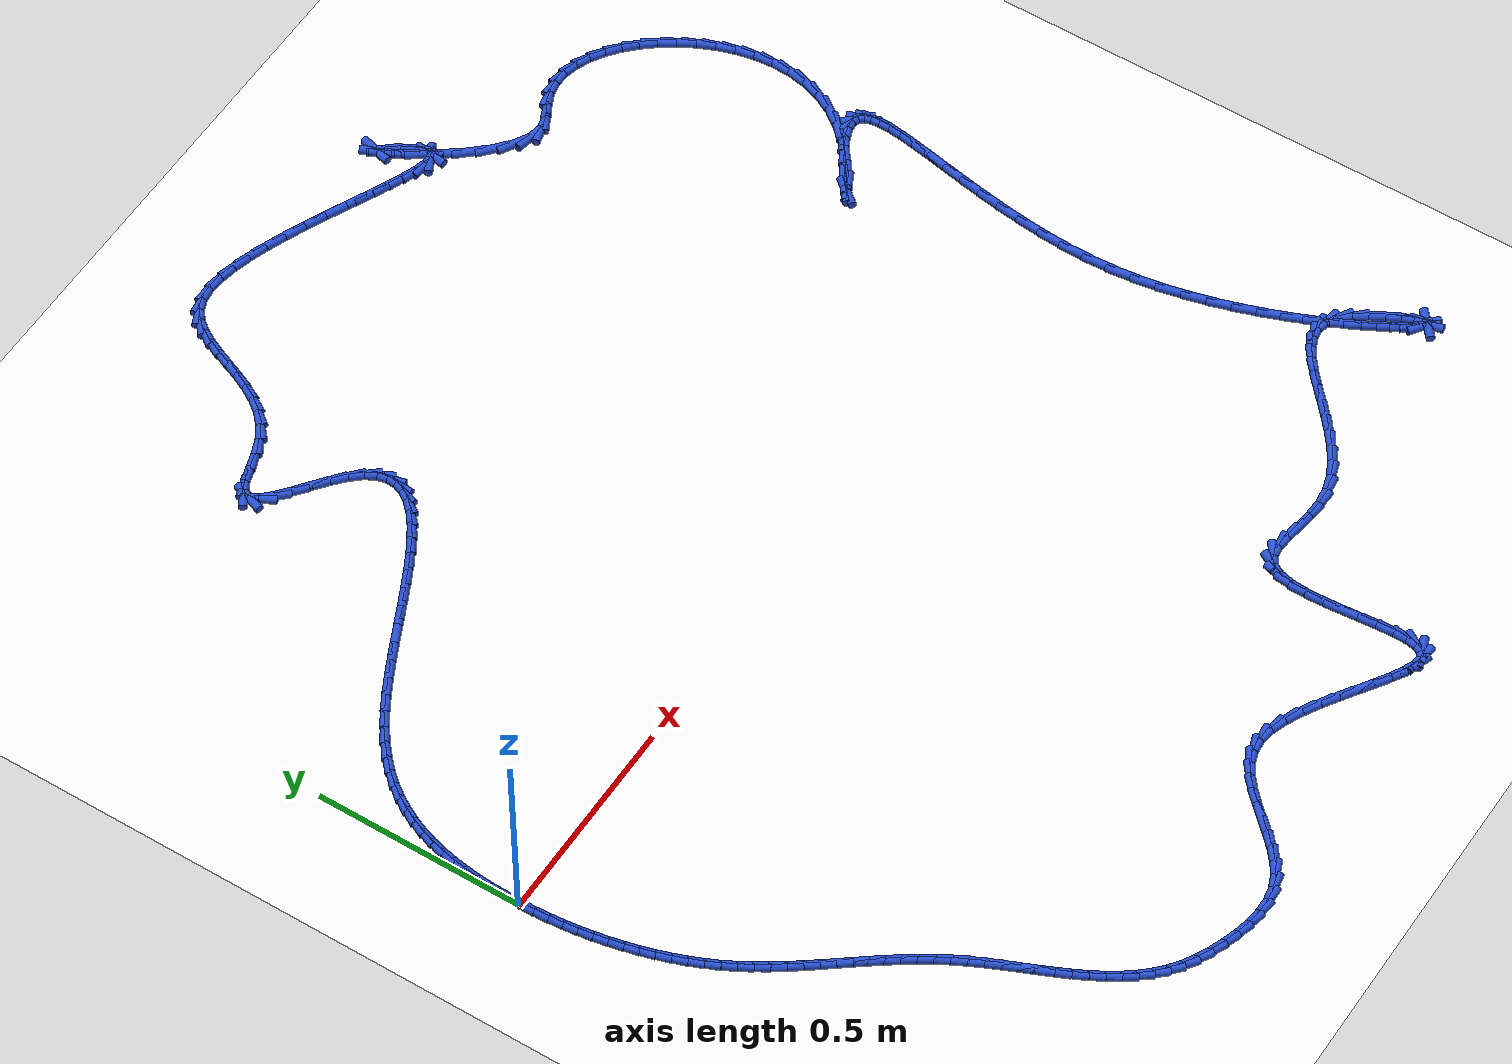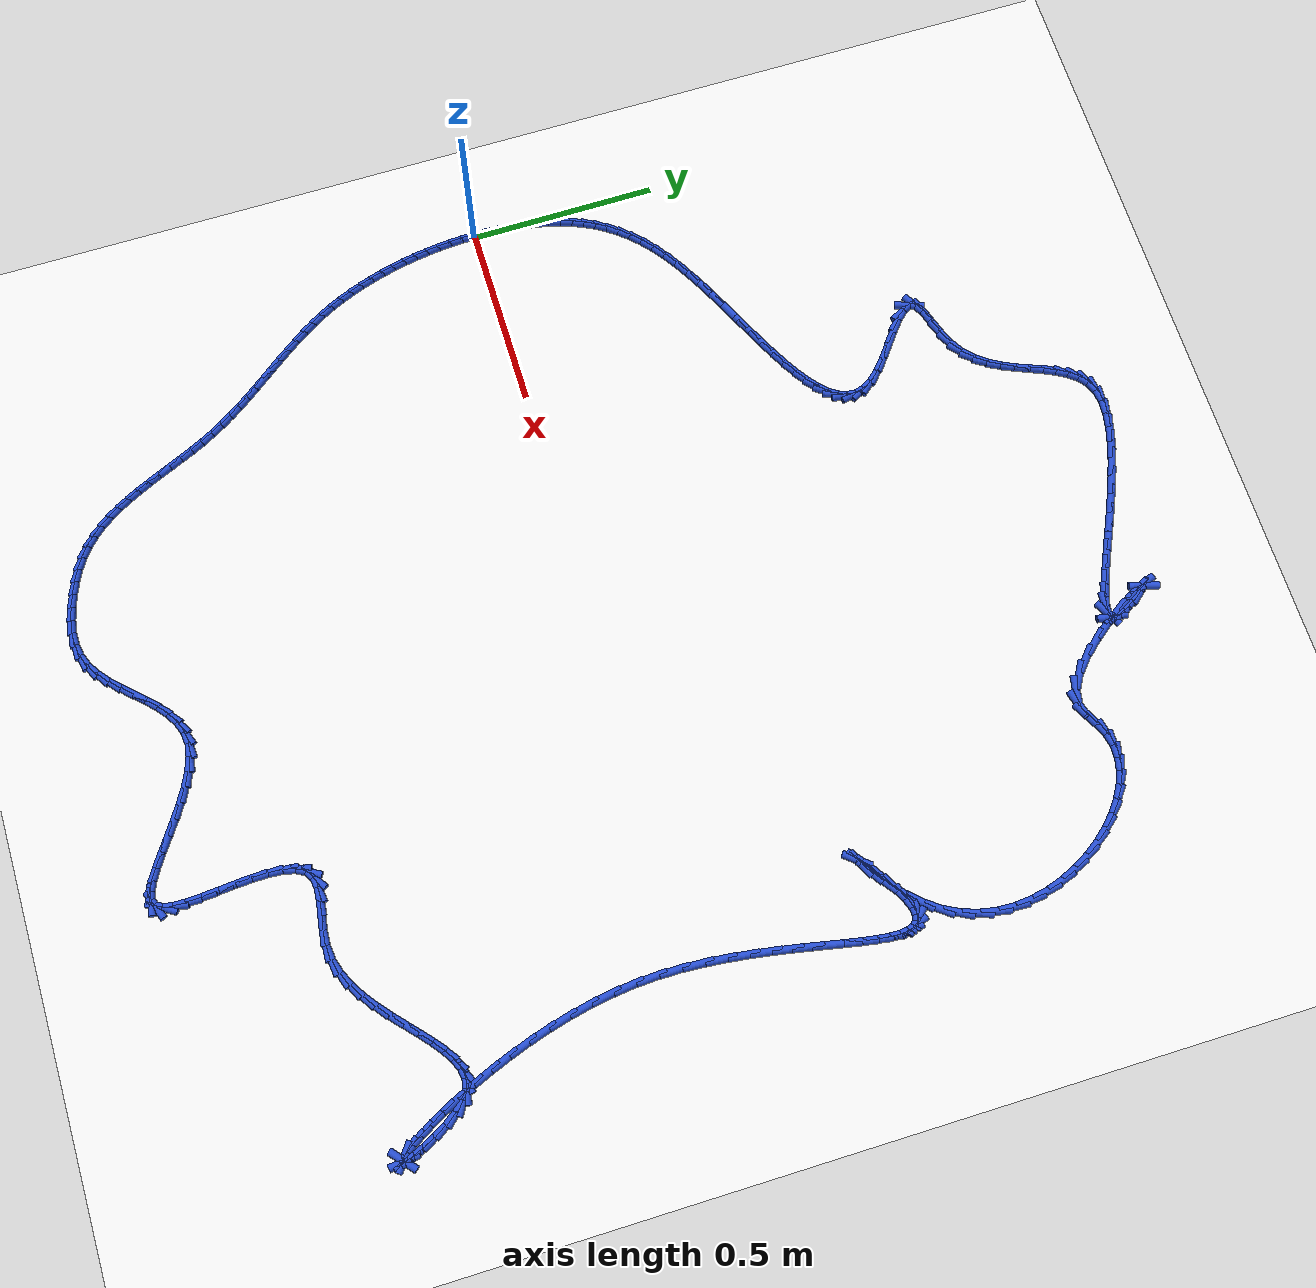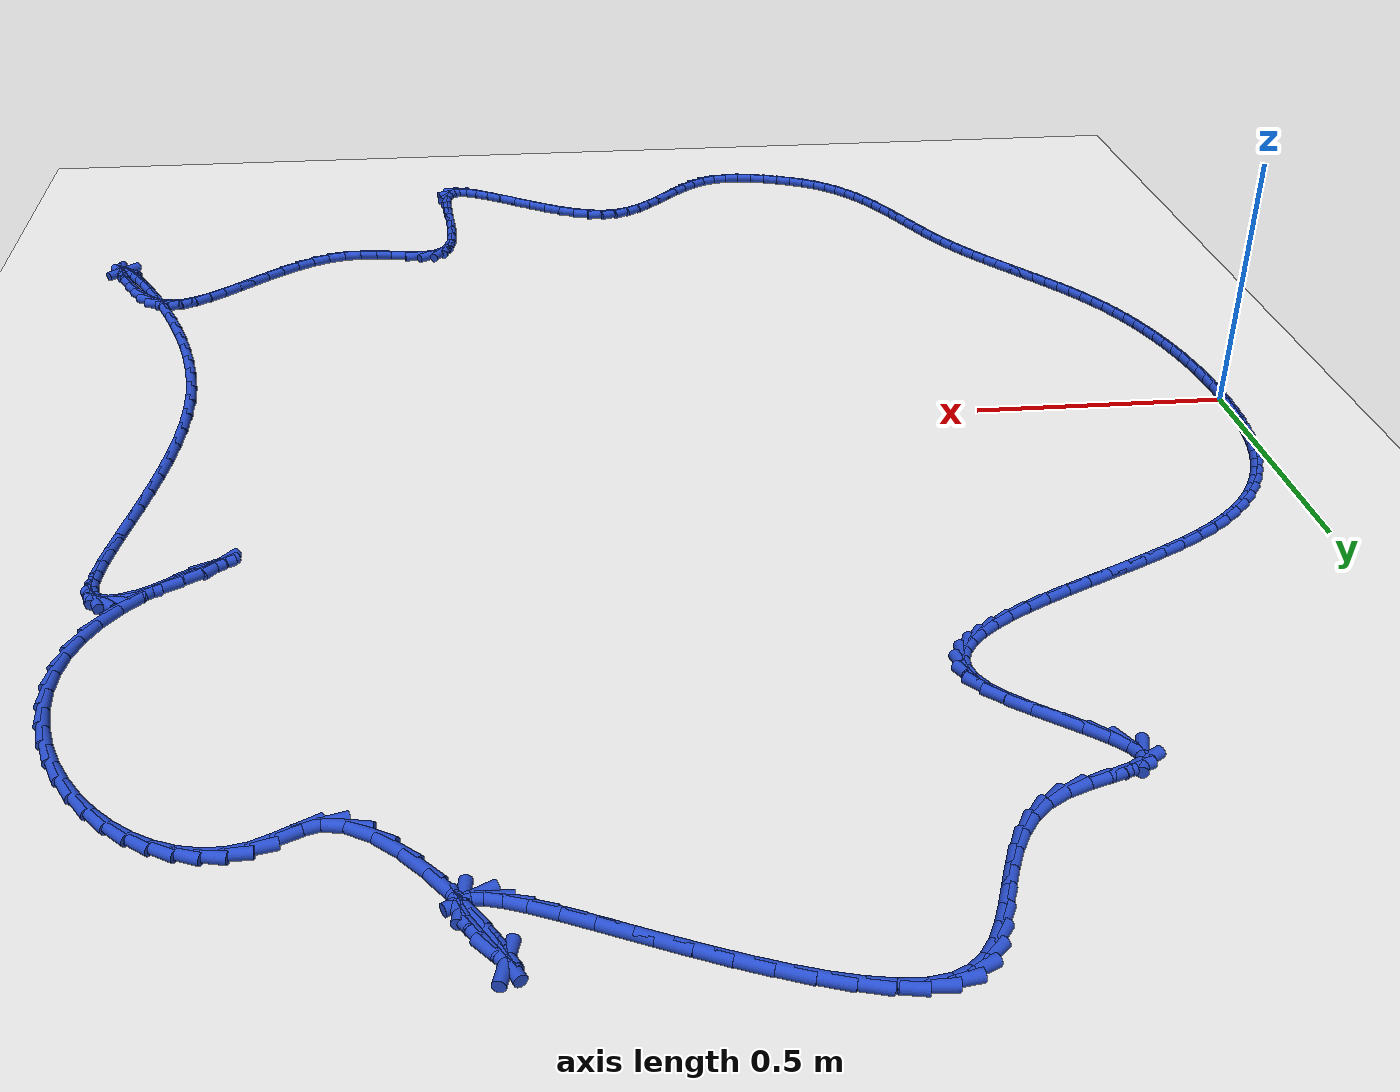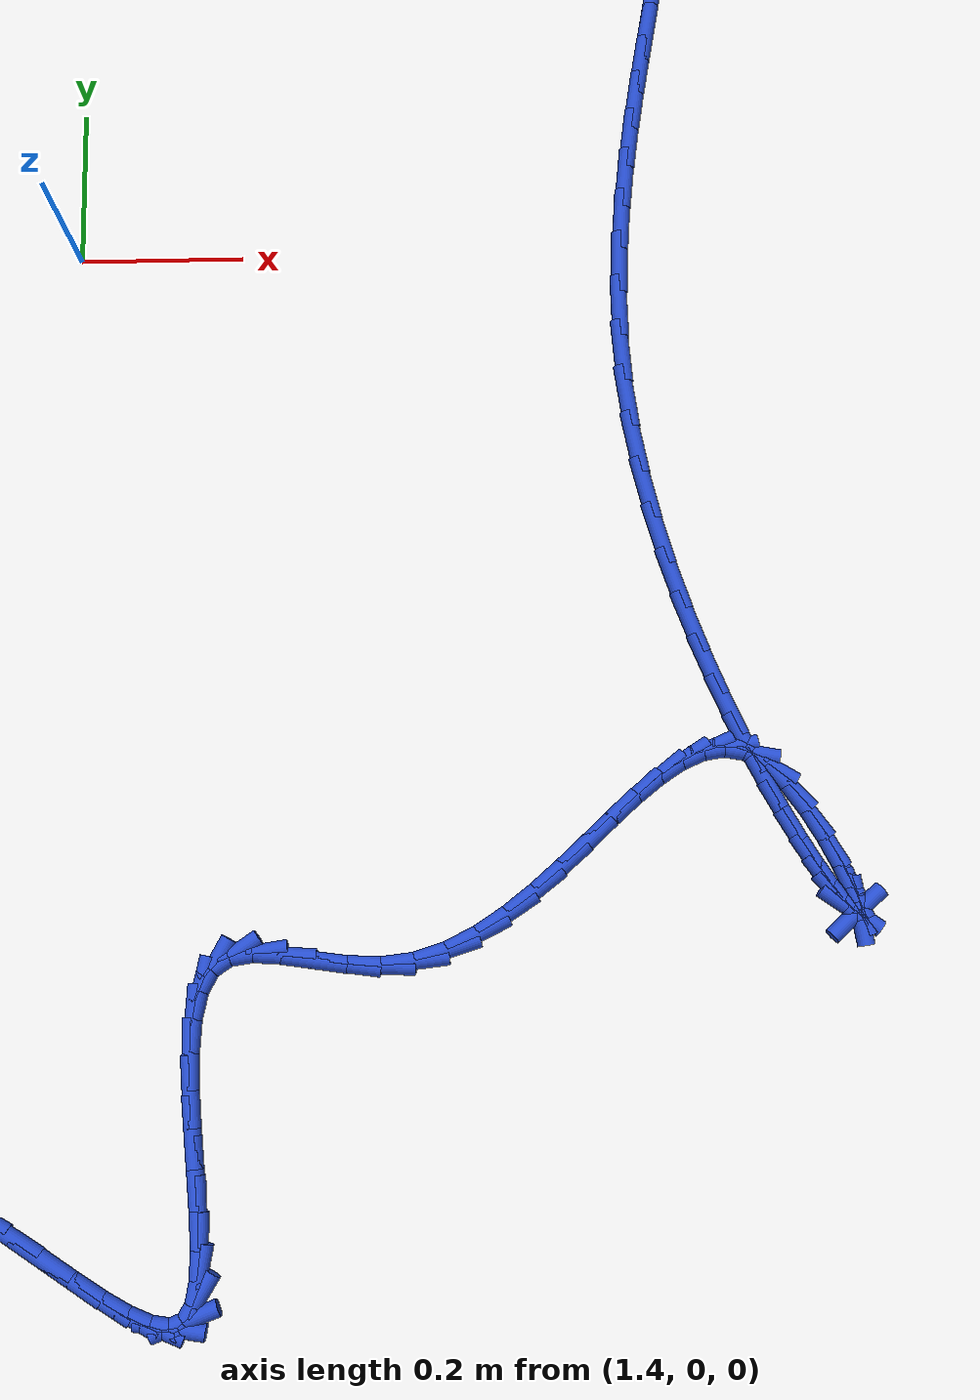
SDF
<sdf version="1.6">
 <world name="default">
  <light name="sun" type="directional">
   <pose>0 0 10 0 -0 0</pose>
   <diffuse>0.8 0.8 0.8 1</diffuse>
   <specular>0.2 0.2 0.2 1</specular>
   <attenuation>
    <range>1000</range>
    <constant>0.9</constant>
    <linear>0.01</linear>
    <quadratic>0.001</quadratic>
   </attenuation>
   <direction>-0.5 0.1 -0.9</direction>
  </light>
  <model name="ground_plane">
   <static>1</static>
   <link name="link">
    <collision name="collision">
     <geometry><plane><normal>0 0 1</normal><size>100 100</size></plane></geometry>
     <surface><friction><ode><mu>100</mu><mu2>50</mu2></ode></friction></surface>
    </collision>
    <visual name="visual">
     <cast_shadows>0</cast_shadows>
     <geometry><plane><normal>0 0 1</normal><size>100 100</size></plane></geometry>
     <material>
      <script><uri>file://media/materials/scripts/gazebo.material</uri><name>Gazebo/WhiteGlow</name></script>
     </material>
    </visual>
   </link>
  </model>
  <gravity>0 0 -9.8</gravity>
  <magnetic_field>6e-06 2.3e-05 -4.2e-05</magnetic_field>
  <atmosphere type="adiabatic"/>
  <physics name="default_physics" default="0" type="ode">
   <max_step_size>0.001</max_step_size>
   <real_time_factor>1</real_time_factor>
   <real_time_update_rate>1000</real_time_update_rate>
  </physics>
  <scene><ambient>0.4 0.4 0.4 1</ambient><background>0.7 0.7 0.7 1</background><shadows>1</shadows></scene>
  <spherical_coordinates>
   <surface_model>EARTH_WGS84</surface_model>
   <latitude_deg>0</latitude_deg>
   <longitude_deg>0</longitude_deg>
   <elevation>0</elevation>
   <heading_deg>0</heading_deg>
  </spherical_coordinates>
  <model name="line">
   <link name="link_0">
    <pose>2.2551405187698492e-17 -4.163336342344337e-17 0.01 0 1.57 1.567977291956659</pose>
    <collision name="collision">
     <geometry><cylinder><radius>0.01</radius><length>0.08</length></cylinder></geometry>
    </collision>
    <visual name="visual">
     <material>
      <script><name>Gazebo/Blue</name><uri>file://media/materials/scripts/gazebo.material</uri></script>
     </material>
     <geometry><cylinder><radius>0.01</radius><length>0.08</length></cylinder></geometry>
    </visual>
   </link>
   <link name="link_1">
    <pose>9.688667654756615e-05 0.034368649362470555 0.01 0 1.57 1.5357420666125772</pose>
    <collision name="collision">
     <geometry><cylinder><radius>0.01</radius><length>0.08</length></cylinder></geometry>
    </collision>
    <visual name="visual">
     <material>
      <script><name>Gazebo/Blue</name><uri>file://media/materials/scripts/gazebo.material</uri></script>
     </material>
     <geometry><cylinder><radius>0.01</radius><length>0.08</length></cylinder></geometry>
    </visual>
   </link>
   <link name="link_2">
    <pose>0.0013037590218697701 0.06878323872105235 0.01 0 1.57 1.4997511849442675</pose>
    <collision name="collision">
     <geometry><cylinder><radius>0.01</radius><length>0.08</length></cylinder></geometry>
    </collision>
    <visual name="visual">
     <material>
      <script><name>Gazebo/Blue</name><uri>file://media/materials/scripts/gazebo.material</uri></script>
     </material>
     <geometry><cylinder><radius>0.01</radius><length>0.08</length></cylinder></geometry>
    </visual>
   </link>
   <link name="link_3">
    <pose>0.003742863435921745 0.10305721224414889 0.01 0 1.57 1.4595072442846933</pose>
    <collision name="collision">
     <geometry><cylinder><radius>0.01</radius><length>0.08</length></cylinder></geometry>
    </collision>
    <visual name="visual">
     <material>
      <script><name>Gazebo/Blue</name><uri>file://media/materials/scripts/gazebo.material</uri></script>
     </material>
     <geometry><cylinder><radius>0.01</radius><length>0.08</length></cylinder></geometry>
    </visual>
   </link>
   <link name="link_4">
    <pose>0.0075364463186585965 0.13700401410016358 0.01 0 1.57 1.414445395928384</pose>
    <collision name="collision">
     <geometry><cylinder><radius>0.01</radius><length>0.08</length></cylinder></geometry>
    </collision>
    <visual name="visual">
     <material>
      <script><name>Gazebo/Blue</name><uri>file://media/materials/scripts/gazebo.material</uri></script>
     </material>
     <geometry><cylinder><radius>0.01</radius><length>0.08</length></cylinder></geometry>
    </visual>
   </link>
   <link name="link_5">
    <pose>0.012806754070035432 0.17043708845749989 0.01 0 1.57 1.3639389401800361</pose>
    <collision name="collision">
     <geometry><cylinder><radius>0.01</radius><length>0.08</length></cylinder></geometry>
    </collision>
    <visual name="visual">
     <material>
      <script><name>Gazebo/Blue</name><uri>file://media/materials/scripts/gazebo.material</uri></script>
     </material>
     <geometry><cylinder><radius>0.01</radius><length>0.08</length></cylinder></geometry>
    </visual>
   </link>
   <link name="link_6">
    <pose>0.01967603309000738 0.20316987948456136 0.01 0 1.57 1.3073162257289797</pose>
    <collision name="collision">
     <geometry><cylinder><radius>0.01</radius><length>0.08</length></cylinder></geometry>
    </collision>
    <visual name="visual">
     <material>
      <script><name>Gazebo/Blue</name><uri>file://media/materials/scripts/gazebo.material</uri></script>
     </material>
     <geometry><cylinder><radius>0.01</radius><length>0.08</length></cylinder></geometry>
    </visual>
   </link>
   <link name="link_7">
    <pose>0.028266549742168974 0.23501593110529378 0.01 0 1.57 1.244111412398534</pose>
    <collision name="collision">
     <geometry><cylinder><radius>0.01</radius><length>0.08</length></cylinder></geometry>
    </collision>
    <visual name="visual">
     <material>
      <script><name>Gazebo/Blue</name><uri>file://media/materials/scripts/gazebo.material</uri></script>
     </material>
     <geometry><cylinder><radius>0.01</radius><length>0.08</length></cylinder></geometry>
    </visual>
   </link>
   <link name="link_8">
    <pose>0.038711257254925004 0.2658421880274798 0.01 0 1.57 1.174938423745464</pose>
    <collision name="collision">
     <geometry><cylinder><radius>0.01</radius><length>0.08</length></cylinder></geometry>
    </collision>
    <visual name="visual">
     <material>
      <script><name>Gazebo/Blue</name><uri>file://media/materials/scripts/gazebo.material</uri></script>
     </material>
     <geometry><cylinder><radius>0.01</radius><length>0.08</length></cylinder></geometry>
    </visual>
   </link>
   <link name="link_9">
    <pose>0.05117137788096851 0.29565685135936204 0.01 0 1.57 1.1009478152931664</pose>
    <collision name="collision">
     <geometry><cylinder><radius>0.01</radius><length>0.08</length></cylinder></geometry>
    </collision>
    <visual name="visual">
     <material>
      <script><name>Gazebo/Blue</name><uri>file://media/materials/scripts/gazebo.material</uri></script>
     </material>
     <geometry><cylinder><radius>0.01</radius><length>0.08</length></cylinder></geometry>
    </visual>
   </link>
   <link name="link_10">
    <pose>0.06581275455062231 0.3244912110955562 0.01 0 1.57 1.0236206646281967</pose>
    <collision name="collision">
     <geometry><cylinder><radius>0.01</radius><length>0.08</length></cylinder></geometry>
    </collision>
    <visual name="visual">
     <material>
      <script><name>Gazebo/Blue</name><uri>file://media/materials/scripts/gazebo.material</uri></script>
     </material>
     <geometry><cylinder><radius>0.01</radius><length>0.08</length></cylinder></geometry>
    </visual>
   </link>
   <link name="link_11">
    <pose>0.08280123019420928 0.35237655723067796 0.01 0 1.57 0.9447071433611985</pose>
    <collision name="collision">
     <geometry><cylinder><radius>0.01</radius><length>0.08</length></cylinder></geometry>
    </collision>
    <visual name="visual">
     <material>
      <script><name>Gazebo/Blue</name><uri>file://media/materials/scripts/gazebo.material</uri></script>
     </material>
     <geometry><cylinder><radius>0.01</radius><length>0.08</length></cylinder></geometry>
    </visual>
   </link>
   <link name="link_12">
    <pose>0.10230264774205214 0.379344179759343 0.01 0 1.57 0.8660531925168482</pose>
    <collision name="collision">
     <geometry><cylinder><radius>0.01</radius><length>0.08</length></cylinder></geometry>
    </collision>
    <visual name="visual">
     <material>
      <script><name>Gazebo/Blue</name><uri>file://media/materials/scripts/gazebo.material</uri></script>
     </material>
     <geometry><cylinder><radius>0.01</radius><length>0.08</length></cylinder></geometry>
    </visual>
   </link>
   <link name="link_13">
    <pose>0.12448285012447369 0.40542536867616685 0.01 0 1.57 0.7894023538734826</pose>
    <collision name="collision">
     <geometry><cylinder><radius>0.01</radius><length>0.08</length></cylinder></geometry>
    </collision>
    <visual name="visual">
     <material>
      <script><name>Gazebo/Blue</name><uri>file://media/materials/scripts/gazebo.material</uri></script>
     </material>
     <geometry><cylinder><radius>0.01</radius><length>0.08</length></cylinder></geometry>
    </visual>
   </link>
   <link name="link_14">
    <pose>0.1495076802717968 0.43065141397576523 0.01 0 1.57 0.7162241377673275</pose>
    <collision name="collision">
     <geometry><cylinder><radius>0.01</radius><length>0.08</length></cylinder></geometry>
    </collision>
    <visual name="visual">
     <material>
      <script><name>Gazebo/Blue</name><uri>file://media/materials/scripts/gazebo.material</uri></script>
     </material>
     <geometry><cylinder><radius>0.01</radius><length>0.08</length></cylinder></geometry>
    </visual>
   </link>
   <link name="link_15">
    <pose>0.1775429811143442 0.4550536056527536 0.01 0 1.57 0.6476082398425609</pose>
    <collision name="collision">
     <geometry><cylinder><radius>0.01</radius><length>0.08</length></cylinder></geometry>
    </collision>
    <visual name="visual">
     <material>
      <script><name>Gazebo/Blue</name><uri>file://media/materials/scripts/gazebo.material</uri></script>
     </material>
     <geometry><cylinder><radius>0.01</radius><length>0.08</length></cylinder></geometry>
    </visual>
   </link>
   <link name="link_16">
    <pose>0.20875459558243875 0.4786632337017478 0.01 0 1.57 0.5847093999354936</pose>
    <collision name="collision">
     <geometry><cylinder><radius>0.01</radius><length>0.08</length></cylinder></geometry>
    </collision>
    <visual name="visual">
     <material>
      <script><name>Gazebo/Blue</name><uri>file://media/materials/scripts/gazebo.material</uri></script>
     </material>
     <geometry><cylinder><radius>0.01</radius><length>0.08</length></cylinder></geometry>
    </visual>
   </link>
   <link name="link_17">
    <pose>0.2432766785114157 0.5015140984469678 0.01 0 1.57 0.5336262199802972</pose>
    <collision name="collision">
     <geometry><cylinder><radius>0.01</radius><length>0.08</length></cylinder></geometry>
    </collision>
    <visual name="visual">
     <material>
      <script><name>Gazebo/Blue</name><uri>file://media/materials/scripts/gazebo.material</uri></script>
     </material>
     <geometry><cylinder><radius>0.01</radius><length>0.08</length></cylinder></geometry>
    </visual>
   </link>
   <link name="link_18">
    <pose>0.2807885145715389 0.5236760350087271 0.01 0 1.57 0.4962218686180734</pose>
    <collision name="collision">
     <geometry><cylinder><radius>0.01</radius><length>0.08</length></cylinder></geometry>
    </collision>
    <visual name="visual">
     <material>
      <script><name>Gazebo/Blue</name><uri>file://media/materials/scripts/gazebo.material</uri></script>
     </material>
     <geometry><cylinder><radius>0.01</radius><length>0.08</length></cylinder></geometry>
    </visual>
   </link>
   <link name="link_19">
    <pose>0.3206288333004343 0.5452458572711841 0.01 0 1.57 0.4699030756825216</pose>
    <collision name="collision">
     <geometry><cylinder><radius>0.01</radius><length>0.08</length></cylinder></geometry>
    </collision>
    <visual name="visual">
     <material>
      <script><name>Gazebo/Blue</name><uri>file://media/materials/scripts/gazebo.material</uri></script>
     </material>
     <geometry><cylinder><radius>0.01</radius><length>0.08</length></cylinder></geometry>
    </visual>
   </link>
   <link name="link_20">
    <pose>0.36212814123439224 0.5663210305443306 0.01 0 1.57 0.45292616012136616</pose>
    <collision name="collision">
     <geometry><cylinder><radius>0.01</radius><length>0.08</length></cylinder></geometry>
    </collision>
    <visual name="visual">
     <material>
      <script><name>Gazebo/Blue</name><uri>file://media/materials/scripts/gazebo.material</uri></script>
     </material>
     <geometry><cylinder><radius>0.01</radius><length>0.08</length></cylinder></geometry>
    </visual>
   </link>
   <link name="link_21">
    <pose>0.40461694490970385 0.5869990201381584 0.01 0 1.57 0.44428829944512876</pose>
    <collision name="collision">
     <geometry><cylinder><radius>0.01</radius><length>0.08</length></cylinder></geometry>
    </collision>
    <visual name="visual">
     <material>
      <script><name>Gazebo/Blue</name><uri>file://media/materials/scripts/gazebo.material</uri></script>
     </material>
     <geometry><cylinder><radius>0.01</radius><length>0.08</length></cylinder></geometry>
    </visual>
   </link>
   <link name="link_22">
    <pose>0.4474257508626597 0.6073772913626589 0.01 0 1.57 0.44359905145111744</pose>
    <collision name="collision">
     <geometry><cylinder><radius>0.01</radius><length>0.08</length></cylinder></geometry>
    </collision>
    <visual name="visual">
     <material>
      <script><name>Gazebo/Blue</name><uri>file://media/materials/scripts/gazebo.material</uri></script>
     </material>
     <geometry><cylinder><radius>0.01</radius><length>0.08</length></cylinder></geometry>
    </visual>
   </link>
   <link name="link_23">
    <pose>0.48988506562955025 0.627553309527824 0.01 0 1.57 0.4510417158108458</pose>
    <collision name="collision">
     <geometry><cylinder><radius>0.01</radius><length>0.08</length></cylinder></geometry>
    </collision>
    <visual name="visual">
     <material>
      <script><name>Gazebo/Blue</name><uri>file://media/materials/scripts/gazebo.material</uri></script>
     </material>
     <geometry><cylinder><radius>0.01</radius><length>0.08</length></cylinder></geometry>
    </visual>
   </link>
   <link name="link_24">
    <pose>0.5313253957466668 0.6476245399436457 0.01 0 1.57 0.4674235573740675</pose>
    <collision name="collision">
     <geometry><cylinder><radius>0.01</radius><length>0.08</length></cylinder></geometry>
    </collision>
    <visual name="visual">
     <material>
      <script><name>Gazebo/Blue</name><uri>file://media/materials/scripts/gazebo.material</uri></script>
     </material>
     <geometry><cylinder><radius>0.01</radius><length>0.08</length></cylinder></geometry>
    </visual>
   </link>
   <link name="link_25">
    <pose>0.5710772477502997 0.667688447920115 0.01 0 1.57 0.49433278869625613</pose>
    <collision name="collision">
     <geometry><cylinder><radius>0.01</radius><length>0.08</length></cylinder></geometry>
    </collision>
    <visual name="visual">
     <material>
      <script><name>Gazebo/Blue</name><uri>file://media/materials/scripts/gazebo.material</uri></script>
     </material>
     <geometry><cylinder><radius>0.01</radius><length>0.08</length></cylinder></geometry>
    </visual>
   </link>
   <link name="link_26">
    <pose>0.6084711281767397 0.6878424987672243 0.01 0 1.57 0.5344461597575991</pose>
    <collision name="collision">
     <geometry><cylinder><radius>0.01</radius><length>0.08</length></cylinder></geometry>
    </collision>
    <visual name="visual">
     <material>
      <script><name>Gazebo/Blue</name><uri>file://media/materials/scripts/gazebo.material</uri></script>
     </material>
     <geometry><cylinder><radius>0.01</radius><length>0.08</length></cylinder></geometry>
    </visual>
   </link>
   <link name="link_27">
    <pose>0.6428375435622776 0.7081841577949649 0.01 0 1.57 0.5920643877317526</pose>
    <collision name="collision">
     <geometry><cylinder><radius>0.01</radius><length>0.08</length></cylinder></geometry>
    </collision>
    <visual name="visual">
     <material>
      <script><name>Gazebo/Blue</name><uri>file://media/materials/scripts/gazebo.material</uri></script>
     </material>
     <geometry><cylinder><radius>0.01</radius><length>0.08</length></cylinder></geometry>
    </visual>
   </link>
   <link name="link_28">
    <pose>0.6735070004432042 0.7288108903133287 0.01 0 1.57 0.6739723901410127</pose>
    <collision name="collision">
     <geometry><cylinder><radius>0.01</radius><length>0.08</length></cylinder></geometry>
    </collision>
    <visual name="visual">
     <material>
      <script><name>Gazebo/Blue</name><uri>file://media/materials/scripts/gazebo.material</uri></script>
     </material>
     <geometry><cylinder><radius>0.01</radius><length>0.08</length></cylinder></geometry>
    </visual>
   </link>
   <link name="link_29">
    <pose>0.69981000535581 0.7498201616323072 0.01 0 1.57 0.7905953803410706</pose>
    <collision name="collision">
     <geometry><cylinder><radius>0.01</radius><length>0.08</length></cylinder></geometry>
    </collision>
    <visual name="visual">
     <material>
      <script><name>Gazebo/Blue</name><uri>file://media/materials/scripts/gazebo.material</uri></script>
     </material>
     <geometry><cylinder><radius>0.01</radius><length>0.08</length></cylinder></geometry>
    </visual>
   </link>
   <link name="link_30">
    <pose>0.7210770648363862 0.7713094370618925 0.01 0 1.57 0.9565843446514154</pose>
    <collision name="collision">
     <geometry><cylinder><radius>0.01</radius><length>0.08</length></cylinder></geometry>
    </collision>
    <visual name="visual">
     <material>
      <script><name>Gazebo/Blue</name><uri>file://media/materials/scripts/gazebo.material</uri></script>
     </material>
     <geometry><cylinder><radius>0.01</radius><length>0.08</length></cylinder></geometry>
    </visual>
   </link>
   <link name="link_31">
    <pose>0.7366386854212231 0.7933761819120759 0.01 0 1.57 1.186882362030653</pose>
    <collision name="collision">
     <geometry><cylinder><radius>0.01</radius><length>0.08</length></cylinder></geometry>
    </collision>
    <visual name="visual">
     <material>
      <script><name>Gazebo/Blue</name><uri>file://media/materials/scripts/gazebo.material</uri></script>
     </material>
     <geometry><cylinder><radius>0.01</radius><length>0.08</length></cylinder></geometry>
    </visual>
   </link>
   <link name="link_32">
    <pose>0.7458253736466116 0.8161178614928493 0.01 0 1.57 1.4799416260970273</pose>
    <collision name="collision">
     <geometry><cylinder><radius>0.01</radius><length>0.08</length></cylinder></geometry>
    </collision>
    <visual name="visual">
     <material>
      <script><name>Gazebo/Blue</name><uri>file://media/materials/scripts/gazebo.material</uri></script>
     </material>
     <geometry><cylinder><radius>0.01</radius><length>0.08</length></cylinder></geometry>
    </visual>
   </link>
   <link name="link_33">
    <pose>0.7479676360488423 0.8396319411142042 0.01 0 1.57 -1.346155946811317</pose>
    <collision name="collision">
     <geometry><cylinder><radius>0.01</radius><length>0.08</length></cylinder></geometry>
    </collision>
    <visual name="visual">
     <material>
      <script><name>Gazebo/Blue</name><uri>file://media/materials/scripts/gazebo.material</uri></script>
     </material>
     <geometry><cylinder><radius>0.01</radius><length>0.08</length></cylinder></geometry>
    </visual>
   </link>
   <link name="link_34">
    <pose>0.7423959791642063 0.864015886086133 0.01 0 1.57 -1.0675937676510234</pose>
    <collision name="collision">
     <geometry><cylinder><radius>0.01</radius><length>0.08</length></cylinder></geometry>
    </collision>
    <visual name="visual">
     <material>
      <script><name>Gazebo/Blue</name><uri>file://media/materials/scripts/gazebo.material</uri></script>
     </material>
     <geometry><cylinder><radius>0.01</radius><length>0.08</length></cylinder></geometry>
    </visual>
   </link>
   <link name="link_35">
    <pose>0.7284409095289941 0.8893671617186265 0.01 0 1.57 -0.8559494949749739</pose>
    <collision name="collision">
     <geometry><cylinder><radius>0.01</radius><length>0.08</length></cylinder></geometry>
    </collision>
    <visual name="visual">
     <material>
      <script><name>Gazebo/Blue</name><uri>file://media/materials/scripts/gazebo.material</uri></script>
     </material>
     <geometry><cylinder><radius>0.01</radius><length>0.08</length></cylinder></geometry>
    </visual>
   </link>
   <link name="link_36">
    <pose>0.7055272210177683 0.91576567558505 0.01 0 1.57 -0.7303945274105144</pose>
    <collision name="collision">
     <geometry><cylinder><radius>0.01</radius><length>0.08</length></cylinder></geometry>
    </collision>
    <visual name="visual">
     <material>
      <script><name>Gazebo/Blue</name><uri>file://media/materials/scripts/gazebo.material</uri></script>
     </material>
     <geometry><cylinder><radius>0.01</radius><length>0.08</length></cylinder></geometry>
    </visual>
   </link>
   <link name="link_37">
    <pose>0.6752438217315034 0.942888344270645 0.01 0 1.57 -0.6747256204293907</pose>
    <collision name="collision">
     <geometry><cylinder><radius>0.01</radius><length>0.08</length></cylinder></geometry>
    </collision>
    <visual name="visual">
     <material>
      <script><name>Gazebo/Blue</name><uri>file://media/materials/scripts/gazebo.material</uri></script>
     </material>
     <geometry><cylinder><radius>0.01</radius><length>0.08</length></cylinder></geometry>
    </visual>
   </link>
   <link name="link_38">
    <pose>0.6413412399643681 0.970009557799453 0.01 0 1.57 -0.6644220891463065</pose>
    <collision name="collision">
     <geometry><cylinder><radius>0.01</radius><length>0.08</length></cylinder></geometry>
    </collision>
    <visual name="visual">
     <material>
      <script><name>Gazebo/Blue</name><uri>file://media/materials/scripts/gazebo.material</uri></script>
     </material>
     <geometry><cylinder><radius>0.01</radius><length>0.08</length></cylinder></geometry>
    </visual>
   </link>
   <link name="link_39">
    <pose>0.6076637925419518 0.9963862413443105 0.01 0 1.57 -0.6990233196383554</pose>
    <collision name="collision">
     <geometry><cylinder><radius>0.01</radius><length>0.08</length></cylinder></geometry>
    </collision>
    <visual name="visual">
     <material>
      <script><name>Gazebo/Blue</name><uri>file://media/materials/scripts/gazebo.material</uri></script>
     </material>
     <geometry><cylinder><radius>0.01</radius><length>0.08</length></cylinder></geometry>
    </visual>
   </link>
   <link name="link_40">
    <pose>0.5780557962898447 1.021275320078055 0.01 0 1.57 -0.8071334936219035</pose>
    <collision name="collision">
     <geometry><cylinder><radius>0.01</radius><length>0.08</length></cylinder></geometry>
    </collision>
    <visual name="visual">
     <material>
      <script><name>Gazebo/Blue</name><uri>file://media/materials/scripts/gazebo.material</uri></script>
     </material>
     <geometry><cylinder><radius>0.01</radius><length>0.08</length></cylinder></geometry>
    </visual>
   </link>
   <link name="link_41">
    <pose>0.5563615680336359 1.043933719173525 0.01 0 1.57 -1.1033430249269622</pose>
    <collision name="collision">
     <geometry><cylinder><radius>0.01</radius><length>0.08</length></cylinder></geometry>
    </collision>
    <visual name="visual">
     <material>
      <script><name>Gazebo/Blue</name><uri>file://media/materials/scripts/gazebo.material</uri></script>
     </material>
     <geometry><cylinder><radius>0.01</radius><length>0.08</length></cylinder></geometry>
    </visual>
   </link>
   <link name="link_42">
    <pose>0.5464254245989147 1.0636183638035563 0.01 0 1.57 1.234013130060733</pose>
    <collision name="collision">
     <geometry><cylinder><radius>0.01</radius><length>0.08</length></cylinder></geometry>
    </collision>
    <visual name="visual">
     <material>
      <script><name>Gazebo/Blue</name><uri>file://media/materials/scripts/gazebo.material</uri></script>
     </material>
     <geometry><cylinder><radius>0.01</radius><length>0.08</length></cylinder></geometry>
    </visual>
   </link>
   <link name="link_43">
    <pose>0.5520236637912591 1.07960777508797 0.01 0 1.57 0.535409955667984</pose>
    <collision name="collision">
     <geometry><cylinder><radius>0.01</radius><length>0.08</length></cylinder></geometry>
    </collision>
    <visual name="visual">
     <material>
      <script><name>Gazebo/Blue</name><uri>file://media/materials/scripts/gazebo.material</uri></script>
     </material>
     <geometry><cylinder><radius>0.01</radius><length>0.08</length></cylinder></geometry>
    </visual>
   </link>
   <link name="link_44">
    <pose>0.5734150313498295 1.092297292176621 0.01 0 1.57 0.33992400352042645</pose>
    <collision name="collision">
     <geometry><cylinder><radius>0.01</radius><length>0.08</length></cylinder></geometry>
    </collision>
    <visual name="visual">
     <material>
      <script><name>Gazebo/Blue</name><uri>file://media/materials/scripts/gazebo.material</uri></script>
     </material>
     <geometry><cylinder><radius>0.01</radius><length>0.08</length></cylinder></geometry>
    </visual>
   </link>
   <link name="link_45">
    <pose>0.6057075738964205 1.1037175942322324 0.01 0 1.57 0.3141571661343411</pose>
    <collision name="collision">
     <geometry><cylinder><radius>0.01</radius><length>0.08</length></cylinder></geometry>
    </collision>
    <visual name="visual">
     <material>
      <script><name>Gazebo/Blue</name><uri>file://media/materials/scripts/gazebo.material</uri></script>
     </material>
     <geometry><cylinder><radius>0.01</radius><length>0.08</length></cylinder></geometry>
    </visual>
   </link>
   <link name="link_46">
    <pose>0.6435997242090881 1.1160294122596626 0.01 0 1.57 0.38249096997888565</pose>
    <collision name="collision">
     <geometry><cylinder><radius>0.01</radius><length>0.08</length></cylinder></geometry>
    </collision>
    <visual name="visual">
     <material>
      <script><name>Gazebo/Blue</name><uri>file://media/materials/scripts/gazebo.material</uri></script>
     </material>
     <geometry><cylinder><radius>0.01</radius><length>0.08</length></cylinder></geometry>
    </visual>
   </link>
   <link name="link_47">
    <pose>0.6817899150658879 1.1313934772637688 0.01 0 1.57 0.5468859215252073</pose>
    <collision name="collision">
     <geometry><cylinder><radius>0.01</radius><length>0.08</length></cylinder></geometry>
    </collision>
    <visual name="visual">
     <material>
      <script><name>Gazebo/Blue</name><uri>file://media/materials/scripts/gazebo.material</uri></script>
     </material>
     <geometry><cylinder><radius>0.01</radius><length>0.08</length></cylinder></geometry>
    </visual>
   </link>
   <link name="link_48">
    <pose>0.715305463447952 1.151798705352107 0.01 0 1.57 0.7466299426678537</pose>
    <collision name="collision">
     <geometry><cylinder><radius>0.01</radius><length>0.08</length></cylinder></geometry>
    </collision>
    <visual name="visual">
     <material>
      <script><name>Gazebo/Blue</name><uri>file://media/materials/scripts/gazebo.material</uri></script>
     </material>
     <geometry><cylinder><radius>0.01</radius><length>0.08</length></cylinder></geometry>
    </visual>
   </link>
   <link name="link_49">
    <pose>0.7428687809344442 1.1773036301664717 0.01 0 1.57 0.9149940455757197</pose>
    <collision name="collision">
     <geometry><cylinder><radius>0.01</radius><length>0.08</length></cylinder></geometry>
    </collision>
    <visual name="visual">
     <material>
      <script><name>Gazebo/Blue</name><uri>file://media/materials/scripts/gazebo.material</uri></script>
     </material>
     <geometry><cylinder><radius>0.01</radius><length>0.08</length></cylinder></geometry>
    </visual>
   </link>
   <link name="link_50">
    <pose>0.7655267228859179 1.2067524549981905 0.01 0 1.57 1.0417562994704492</pose>
    <collision name="collision">
     <geometry><cylinder><radius>0.01</radius><length>0.08</length></cylinder></geometry>
    </collision>
    <visual name="visual">
     <material>
      <script><name>Gazebo/Blue</name><uri>file://media/materials/scripts/gazebo.material</uri></script>
     </material>
     <geometry><cylinder><radius>0.01</radius><length>0.08</length></cylinder></geometry>
    </visual>
   </link>
   <link name="link_51">
    <pose>0.7843622983292439 1.2389704958268641 0.01 0 1.57 1.1264978375422985</pose>
    <collision name="collision">
     <geometry><cylinder><radius>0.01</radius><length>0.08</length></cylinder></geometry>
    </collision>
    <visual name="visual">
     <material>
      <script><name>Gazebo/Blue</name><uri>file://media/materials/scripts/gazebo.material</uri></script>
     </material>
     <geometry><cylinder><radius>0.01</radius><length>0.08</length></cylinder></geometry>
    </visual>
   </link>
   <link name="link_52">
    <pose>0.8004585162912932 1.2727830686320942 0.01 0 1.57 1.1716234936725571</pose>
    <collision name="collision">
     <geometry><cylinder><radius>0.01</radius><length>0.08</length></cylinder></geometry>
    </collision>
    <visual name="visual">
     <material>
      <script><name>Gazebo/Blue</name><uri>file://media/materials/scripts/gazebo.material</uri></script>
     </material>
     <geometry><cylinder><radius>0.01</radius><length>0.08</length></cylinder></geometry>
    </visual>
   </link>
   <link name="link_53">
    <pose>0.8148983857989359 1.3070154893934816 0.01 0 1.57 1.1781059020513198</pose>
    <collision name="collision">
     <geometry><cylinder><radius>0.01</radius><length>0.08</length></cylinder></geometry>
    </collision>
    <visual name="visual">
     <material>
      <script><name>Gazebo/Blue</name><uri>file://media/materials/scripts/gazebo.material</uri></script>
     </material>
     <geometry><cylinder><radius>0.01</radius><length>0.08</length></cylinder></geometry>
    </visual>
   </link>
   <link name="link_54">
    <pose>0.8287649158790432 1.3404930740906267 0.01 0 1.57 1.1432190507362112</pose>
    <collision name="collision">
     <geometry><cylinder><radius>0.01</radius><length>0.08</length></cylinder></geometry>
    </collision>
    <visual name="visual">
     <material>
      <script><name>Gazebo/Blue</name><uri>file://media/materials/scripts/gazebo.material</uri></script>
     </material>
     <geometry><cylinder><radius>0.01</radius><length>0.08</length></cylinder></geometry>
    </visual>
   </link>
   <link name="link_55">
    <pose>0.8431411155584857 1.3720411387031313 0.01 0 1.57 1.0592296349108181</pose>
    <collision name="collision">
     <geometry><cylinder><radius>0.01</radius><length>0.08</length></cylinder></geometry>
    </collision>
    <visual name="visual">
     <material>
      <script><name>Gazebo/Blue</name><uri>file://media/materials/scripts/gazebo.material</uri></script>
     </material>
     <geometry><cylinder><radius>0.01</radius><length>0.08</length></cylinder></geometry>
    </visual>
   </link>
   <link name="link_56">
    <pose>0.8591099938641339 1.400484999210596 0.01 0 1.57 0.913643155080199</pose>
    <collision name="collision">
     <geometry><cylinder><radius>0.01</radius><length>0.08</length></cylinder></geometry>
    </collision>
    <visual name="visual">
     <material>
      <script><name>Gazebo/Blue</name><uri>file://media/materials/scripts/gazebo.material</uri></script>
     </material>
     <geometry><cylinder><radius>0.01</radius><length>0.08</length></cylinder></geometry>
    </visual>
   </link>
   <link name="link_57">
    <pose>0.8777545598228587 1.4246499715926215 0.01 0 1.57 0.6958440394480391</pose>
    <collision name="collision">
     <geometry><cylinder><radius>0.01</radius><length>0.08</length></cylinder></geometry>
    </collision>
    <visual name="visual">
     <material>
      <script><name>Gazebo/Blue</name><uri>file://media/materials/scripts/gazebo.material</uri></script>
     </material>
     <geometry><cylinder><radius>0.01</radius><length>0.08</length></cylinder></geometry>
    </visual>
   </link>
   <link name="link_58">
    <pose>0.9001578224615306 1.4433613718288099 0.01 0 1.57 0.4174359137270078</pose>
    <collision name="collision">
     <geometry><cylinder><radius>0.01</radius><length>0.08</length></cylinder></geometry>
    </collision>
    <visual name="visual">
     <material>
      <script><name>Gazebo/Blue</name><uri>file://media/materials/scripts/gazebo.material</uri></script>
     </material>
     <geometry><cylinder><radius>0.01</radius><length>0.08</length></cylinder></geometry>
    </visual>
   </link>
   <link name="link_59">
    <pose>0.9274027800360201 1.4554445274772732 0.01 0 1.57 0.1415273474096309</pose>
    <collision name="collision">
     <geometry><cylinder><radius>0.01</radius><length>0.08</length></cylinder></geometry>
    </collision>
    <visual name="visual">
     <material>
      <script><name>Gazebo/Blue</name><uri>file://media/materials/scripts/gazebo.material</uri></script>
     </material>
     <geometry><cylinder><radius>0.01</radius><length>0.08</length></cylinder></geometry>
    </visual>
   </link>
   <link name="link_60">
    <pose>0.9602062802843765 1.4601183672575422 0.01 0 1.57 -0.055191477168384996</pose>
    <collision name="collision">
     <geometry><cylinder><radius>0.01</radius><length>0.08</length></cylinder></geometry>
    </collision>
    <visual name="visual">
     <material>
      <script><name>Gazebo/Blue</name><uri>file://media/materials/scripts/gazebo.material</uri></script>
     </material>
     <geometry><cylinder><radius>0.01</radius><length>0.08</length></cylinder></geometry>
    </visual>
   </link>
   <link name="link_61">
    <pose>0.9979538951214667 1.4580329026943528 0.01 0 1.57 -0.18619947121549568</pose>
    <collision name="collision">
     <geometry><cylinder><radius>0.01</radius><length>0.08</length></cylinder></geometry>
    </collision>
    <visual name="visual">
     <material>
      <script><name>Gazebo/Blue</name><uri>file://media/materials/scripts/gazebo.material</uri></script>
     </material>
     <geometry><cylinder><radius>0.01</radius><length>0.08</length></cylinder></geometry>
    </visual>
   </link>
   <link name="link_62">
    <pose>1.0397287248588571 1.4501632934921107 0.01 0 1.57 -0.2752953349042242</pose>
    <collision name="collision">
     <geometry><cylinder><radius>0.01</radius><length>0.08</length></cylinder></geometry>
    </collision>
    <visual name="visual">
     <material>
      <script><name>Gazebo/Blue</name><uri>file://media/materials/scripts/gazebo.material</uri></script>
     </material>
     <geometry><cylinder><radius>0.01</radius><length>0.08</length></cylinder></geometry>
    </visual>
   </link>
   <link name="link_63">
    <pose>1.0846138698081158 1.4374846993552204 0.01 0 1.57 -0.337335518957042</pose>
    <collision name="collision">
     <geometry><cylinder><radius>0.01</radius><length>0.08</length></cylinder></geometry>
    </collision>
    <visual name="visual">
     <material>
      <script><name>Gazebo/Blue</name><uri>file://media/materials/scripts/gazebo.material</uri></script>
     </material>
     <geometry><cylinder><radius>0.01</radius><length>0.08</length></cylinder></geometry>
    </visual>
   </link>
   <link name="link_64">
    <pose>1.1316924302808098 1.4209722799880873 0.01 0 1.57 -0.38102424786872485</pose>
    <collision name="collision">
     <geometry><cylinder><radius>0.01</radius><length>0.08</length></cylinder></geometry>
    </collision>
    <visual name="visual">
     <material>
      <script><name>Gazebo/Blue</name><uri>file://media/materials/scripts/gazebo.material</uri></script>
     </material>
     <geometry><cylinder><radius>0.01</radius><length>0.08</length></cylinder></geometry>
    </visual>
   </link>
   <link name="link_65">
    <pose>1.1800475065885059 1.4016011950951162 0.01 0 1.57 -0.4114091722559815</pose>
    <collision name="collision">
     <geometry><cylinder><radius>0.01</radius><length>0.08</length></cylinder></geometry>
    </collision>
    <visual name="visual">
     <material>
      <script><name>Gazebo/Blue</name><uri>file://media/materials/scripts/gazebo.material</uri></script>
     </material>
     <geometry><cylinder><radius>0.01</radius><length>0.08</length></cylinder></geometry>
    </visual>
   </link>
   <link name="link_66">
    <pose>1.2287621990427713 1.3803466043807124 0.01 0 1.57 -0.4313191744088357</pose>
    <collision name="collision">
     <geometry><cylinder><radius>0.01</radius><length>0.08</length></cylinder></geometry>
    </collision>
    <visual name="visual">
     <material>
      <script><name>Gazebo/Blue</name><uri>file://media/materials/scripts/gazebo.material</uri></script>
     </material>
     <geometry><cylinder><radius>0.01</radius><length>0.08</length></cylinder></geometry>
    </visual>
   </link>
   <link name="link_67">
    <pose>1.2769196079551728 1.3581836675492815 0.01 0 1.57 -0.4420770451316241</pose>
    <collision name="collision">
     <geometry><cylinder><radius>0.01</radius><length>0.08</length></cylinder></geometry>
    </collision>
    <visual name="visual">
     <material>
      <script><name>Gazebo/Blue</name><uri>file://media/materials/scripts/gazebo.material</uri></script>
     </material>
     <geometry><cylinder><radius>0.01</radius><length>0.08</length></cylinder></geometry>
    </visual>
   </link>
   <link name="link_68">
    <pose>1.3236028336372785 1.3360875443052282 0.01 0 1.57 -0.44373165430215145</pose>
    <collision name="collision">
     <geometry><cylinder><radius>0.01</radius><length>0.08</length></cylinder></geometry>
    </collision>
    <visual name="visual">
     <material>
      <script><name>Gazebo/Blue</name><uri>file://media/materials/scripts/gazebo.material</uri></script>
     </material>
     <geometry><cylinder><radius>0.01</radius><length>0.08</length></cylinder></geometry>
    </visual>
   </link>
   <link name="link_69">
    <pose>1.3678949764006545 1.315033394352957 0.01 0 1.57 -0.43484396868742275</pose>
    <collision name="collision">
     <geometry><cylinder><radius>0.01</radius><length>0.08</length></cylinder></geometry>
    </collision>
    <visual name="visual">
     <material>
      <script><name>Gazebo/Blue</name><uri>file://media/materials/scripts/gazebo.material</uri></script>
     </material>
     <geometry><cylinder><radius>0.01</radius><length>0.08</length></cylinder></geometry>
    </visual>
   </link>
   <link name="link_70">
    <pose>1.408879136556868 1.2959963773968743 0.01 0 1.57 -0.41155478175469357</pose>
    <collision name="collision">
     <geometry><cylinder><radius>0.01</radius><length>0.08</length></cylinder></geometry>
    </collision>
    <visual name="visual">
     <material>
      <script><name>Gazebo/Blue</name><uri>file://media/materials/scripts/gazebo.material</uri></script>
     </material>
     <geometry><cylinder><radius>0.01</radius><length>0.08</length></cylinder></geometry>
    </visual>
   </link>
   <link name="link_71">
    <pose>1.445638414417487 1.2799516531413841 0.01 0 1.57 -0.36487660915361647</pose>
    <collision name="collision">
     <geometry><cylinder><radius>0.01</radius><length>0.08</length></cylinder></geometry>
    </collision>
    <visual name="visual">
     <material>
      <script><name>Gazebo/Blue</name><uri>file://media/materials/scripts/gazebo.material</uri></script>
     </material>
     <geometry><cylinder><radius>0.01</radius><length>0.08</length></cylinder></geometry>
    </visual>
   </link>
   <link name="link_72">
    <pose>1.4772559102940783 1.267874381290892 0.01 0 1.57 -0.27221730299844576</pose>
    <collision name="collision">
     <geometry><cylinder><radius>0.01</radius><length>0.08</length></cylinder></geometry>
    </collision>
    <visual name="visual">
     <material>
      <script><name>Gazebo/Blue</name><uri>file://media/materials/scripts/gazebo.material</uri></script>
     </material>
     <geometry><cylinder><radius>0.01</radius><length>0.08</length></cylinder></geometry>
    </visual>
   </link>
   <link name="link_73">
    <pose>1.5028147244982089 1.260739721549803 0.01 0 1.57 -0.06538975457168264</pose>
    <collision name="collision">
     <geometry><cylinder><radius>0.01</radius><length>0.08</length></cylinder></geometry>
    </collision>
    <visual name="visual">
     <material>
      <script><name>Gazebo/Blue</name><uri>file://media/materials/scripts/gazebo.material</uri></script>
     </material>
     <geometry><cylinder><radius>0.01</radius><length>0.08</length></cylinder></geometry>
    </visual>
   </link>
   <link name="link_74">
    <pose>1.5213979573414456 1.2595228336225222 0.01 0 1.57 0.48808455209873003</pose>
    <collision name="collision">
     <geometry><cylinder><radius>0.01</radius><length>0.08</length></cylinder></geometry>
    </collision>
    <visual name="visual">
     <material>
      <script><name>Gazebo/Blue</name><uri>file://media/materials/scripts/gazebo.material</uri></script>
     </material>
     <geometry><cylinder><radius>0.01</radius><length>0.08</length></cylinder></geometry>
    </visual>
   </link>
   <link name="link_75">
    <pose>1.532088709135356 1.2651988772134546 0.01 0 1.57 1.4327728302426603</pose>
    <collision name="collision">
     <geometry><cylinder><radius>0.01</radius><length>0.08</length></cylinder></geometry>
    </collision>
    <visual name="visual">
     <material>
      <script><name>Gazebo/Blue</name><uri>file://media/materials/scripts/gazebo.material</uri></script>
     </material>
     <geometry><cylinder><radius>0.01</radius><length>0.08</length></cylinder></geometry>
    </visual>
   </link>
   <link name="link_76">
    <pose>1.5339700801915075 1.2787430120270062 0.01 0 1.57 -1.233750508250868</pose>
    <collision name="collision">
     <geometry><cylinder><radius>0.01</radius><length>0.08</length></cylinder></geometry>
    </collision>
    <visual name="visual">
     <material>
      <script><name>Gazebo/Blue</name><uri>file://media/materials/scripts/gazebo.material</uri></script>
     </material>
     <geometry><cylinder><radius>0.01</radius><length>0.08</length></cylinder></geometry>
    </visual>
   </link>
   <link name="link_77">
    <pose>1.5261251708214667 1.301130397767581 0.01 0 1.57 -1.0558645574576324</pose>
    <collision name="collision">
     <geometry><cylinder><radius>0.01</radius><length>0.08</length></cylinder></geometry>
    </collision>
    <visual name="visual">
     <material>
      <script><name>Gazebo/Blue</name><uri>file://media/materials/scripts/gazebo.material</uri></script>
     </material>
     <geometry><cylinder><radius>0.01</radius><length>0.08</length></cylinder></geometry>
    </visual>
   </link>
   <link name="link_78">
    <pose>1.5087342437098061 1.3318644803971376 0.01 0 1.57 -0.9763208478459828</pose>
    <collision name="collision">
     <geometry><cylinder><radius>0.01</radius><length>0.08</length></cylinder></geometry>
    </collision>
    <visual name="visual">
     <material>
      <script><name>Gazebo/Blue</name><uri>file://media/materials/scripts/gazebo.material</uri></script>
     </material>
     <geometry><cylinder><radius>0.01</radius><length>0.08</length></cylinder></geometry>
    </visual>
   </link>
   <link name="link_79">
    <pose>1.4891869022287192 1.3607782268081703 0.01 0 1.57 -0.8588360218117883</pose>
    <collision name="collision">
     <geometry><cylinder><radius>0.01</radius><length>0.08</length></cylinder></geometry>
    </collision>
    <visual name="visual">
     <material>
      <script><name>Gazebo/Blue</name><uri>file://media/materials/scripts/gazebo.material</uri></script>
     </material>
     <geometry><cylinder><radius>0.01</radius><length>0.08</length></cylinder></geometry>
    </visual>
   </link>
   <link name="link_80">
    <pose>1.4772433302474652 1.3746187380056363 0.01 0 1.57 1.309518038997576</pose>
    <collision name="collision">
     <geometry><cylinder><radius>0.01</radius><length>0.08</length></cylinder></geometry>
    </collision>
    <visual name="visual">
     <material>
      <script><name>Gazebo/Blue</name><uri>file://media/materials/scripts/gazebo.material</uri></script>
     </material>
     <geometry><cylinder><radius>0.01</radius><length>0.08</length></cylinder></geometry>
    </visual>
   </link>
   <link name="link_81">
    <pose>1.4760504526278317 1.3701575605409764 0.01 0 1.57 -1.1655462652399033</pose>
    <collision name="collision">
     <geometry><cylinder><radius>0.01</radius><length>0.08</length></cylinder></geometry>
    </collision>
    <visual name="visual">
     <material>
      <script><name>Gazebo/Blue</name><uri>file://media/materials/scripts/gazebo.material</uri></script>
     </material>
     <geometry><cylinder><radius>0.01</radius><length>0.08</length></cylinder></geometry>
    </visual>
   </link>
   <link name="link_82">
    <pose>1.4843111943444742 1.3509015537082 0.01 0 1.57 -1.0779919686023898</pose>
    <collision name="collision">
     <geometry><cylinder><radius>0.01</radius><length>0.08</length></cylinder></geometry>
    </collision>
    <visual name="visual">
     <material>
      <script><name>Gazebo/Blue</name><uri>file://media/materials/scripts/gazebo.material</uri></script>
     </material>
     <geometry><cylinder><radius>0.01</radius><length>0.08</length></cylinder></geometry>
    </visual>
   </link>
   <link name="link_83">
    <pose>1.5006462802699212 1.3204821590266422 0.01 0 1.57 -1.0253671478310846</pose>
    <collision name="collision">
     <geometry><cylinder><radius>0.01</radius><length>0.08</length></cylinder></geometry>
    </collision>
    <visual name="visual">
     <material>
      <script><name>Gazebo/Blue</name><uri>file://media/materials/scripts/gazebo.material</uri></script>
     </material>
     <geometry><cylinder><radius>0.01</radius><length>0.08</length></cylinder></geometry>
    </visual>
   </link>
   <link name="link_84">
    <pose>1.523676435276702 1.2825308180156376 0.01 0 1.57 -0.9754732832924256</pose>
    <collision name="collision">
     <geometry><cylinder><radius>0.01</radius><length>0.08</length></cylinder></geometry>
    </collision>
    <visual name="visual">
     <material>
      <script><name>Gazebo/Blue</name><uri>file://media/materials/scripts/gazebo.material</uri></script>
     </material>
     <geometry><cylinder><radius>0.01</radius><length>0.08</length></cylinder></geometry>
    </visual>
   </link>
   <link name="link_85">
    <pose>1.5520223842373457 1.240678972194521 0.01 0 1.57 -0.9168665719652358</pose>
    <collision name="collision">
     <geometry><cylinder><radius>0.01</radius><length>0.08</length></cylinder></geometry>
    </collision>
    <visual name="visual">
     <material>
      <script><name>Gazebo/Blue</name><uri>file://media/materials/scripts/gazebo.material</uri></script>
     </material>
     <geometry><cylinder><radius>0.01</radius><length>0.08</length></cylinder></geometry>
    </visual>
   </link>
   <link name="link_86">
    <pose>1.5843048520243814 1.198558063082627 0.01 0 1.57 -0.8385940289771048</pose>
    <collision name="collision">
     <geometry><cylinder><radius>0.01</radius><length>0.08</length></cylinder></geometry>
    </collision>
    <visual name="visual">
     <material>
      <script><name>Gazebo/Blue</name><uri>file://media/materials/scripts/gazebo.material</uri></script>
     </material>
     <geometry><cylinder><radius>0.01</radius><length>0.08</length></cylinder></geometry>
    </visual>
   </link>
   <link name="link_87">
    <pose>1.6191445635103383 1.1597995321992904 0.01 0 1.57 -0.7227358572964344</pose>
    <collision name="collision">
     <geometry><cylinder><radius>0.01</radius><length>0.08</length></cylinder></geometry>
    </collision>
    <visual name="visual">
     <material>
      <script><name>Gazebo/Blue</name><uri>file://media/materials/scripts/gazebo.material</uri></script>
     </material>
     <geometry><cylinder><radius>0.01</radius><length>0.08</length></cylinder></geometry>
    </visual>
   </link>
   <link name="link_88">
    <pose>1.6551622435677456 1.1280348210638462 0.01 0 1.57 -0.5331954214277275</pose>
    <collision name="collision">
     <geometry><cylinder><radius>0.01</radius><length>0.08</length></cylinder></geometry>
    </collision>
    <visual name="visual">
     <material>
      <script><name>Gazebo/Blue</name><uri>file://media/materials/scripts/gazebo.material</uri></script>
     </material>
     <geometry><cylinder><radius>0.01</radius><length>0.08</length></cylinder></geometry>
    </visual>
   </link>
   <link name="link_89">
    <pose>1.6909786170691337 1.1068953711956295 0.01 0 1.57 -0.19839489617529274</pose>
    <collision name="collision">
     <geometry><cylinder><radius>0.01</radius><length>0.08</length></cylinder></geometry>
    </collision>
    <visual name="visual">
     <material>
      <script><name>Gazebo/Blue</name><uri>file://media/materials/scripts/gazebo.material</uri></script>
     </material>
     <geometry><cylinder><radius>0.01</radius><length>0.08</length></cylinder></geometry>
    </visual>
   </link>
   <link name="link_90">
    <pose>1.7252144088870303 1.1000126241139747 0.01 0 1.57 0.2682369286196447</pose>
    <collision name="collision">
     <geometry><cylinder><radius>0.01</radius><length>0.08</length></cylinder></geometry>
    </collision>
    <visual name="visual">
     <material>
      <script><name>Gazebo/Blue</name><uri>file://media/materials/scripts/gazebo.material</uri></script>
     </material>
     <geometry><cylinder><radius>0.01</radius><length>0.08</length></cylinder></geometry>
    </visual>
   </link>
   <link name="link_91">
    <pose>1.7570063198343666 1.108750978822055 0.01 0 1.57 0.4954996933951386</pose>
    <collision name="collision">
     <geometry><cylinder><radius>0.01</radius><length>0.08</length></cylinder></geometry>
    </collision>
    <visual name="visual">
     <material>
      <script><name>Gazebo/Blue</name><uri>file://media/materials/scripts/gazebo.material</uri></script>
     </material>
     <geometry><cylinder><radius>0.01</radius><length>0.08</length></cylinder></geometry>
    </visual>
   </link>
   <link name="link_92">
    <pose>1.787584333638353 1.125277581130717 0.01 0 1.57 0.4306012057078743</pose>
    <collision name="collision">
     <geometry><cylinder><radius>0.01</radius><length>0.08</length></cylinder></geometry>
    </collision>
    <visual name="visual">
     <material>
      <script><name>Gazebo/Blue</name><uri>file://media/materials/scripts/gazebo.material</uri></script>
     </material>
     <geometry><cylinder><radius>0.01</radius><length>0.08</length></cylinder></geometry>
    </visual>
   </link>
   <link name="link_93">
    <pose>1.8186808127239034 1.1395617140799776 0.01 0 1.57 0.2015976093520429</pose>
    <collision name="collision">
     <geometry><cylinder><radius>0.01</radius><length>0.08</length></cylinder></geometry>
    </collision>
    <visual name="visual">
     <material>
      <script><name>Gazebo/Blue</name><uri>file://media/materials/scripts/gazebo.material</uri></script>
     </material>
     <geometry><cylinder><radius>0.01</radius><length>0.08</length></cylinder></geometry>
    </visual>
   </link>
   <link name="link_94">
    <pose>1.851053698110514 1.1461778847529427 0.01 0 1.57 -0.024871711894914314</pose>
    <collision name="collision">
     <geometry><cylinder><radius>0.01</radius><length>0.08</length></cylinder></geometry>
    </collision>
    <visual name="visual">
     <material>
      <script><name>Gazebo/Blue</name><uri>file://media/materials/scripts/gazebo.material</uri></script>
     </material>
     <geometry><cylinder><radius>0.01</radius><length>0.08</length></cylinder></geometry>
    </visual>
   </link>
   <link name="link_95">
    <pose>1.8842652148252643 1.1453516871080744 0.01 0 1.57 -0.22558317602559938</pose>
    <collision name="collision">
     <geometry><cylinder><radius>0.01</radius><length>0.08</length></cylinder></geometry>
    </collision>
    <visual name="visual">
     <material>
      <script><name>Gazebo/Blue</name><uri>file://media/materials/scripts/gazebo.material</uri></script>
     </material>
     <geometry><cylinder><radius>0.01</radius><length>0.08</length></cylinder></geometry>
    </visual>
   </link>
   <link name="link_96">
    <pose>1.917804355999808 1.13765481719306 0.01 0 1.57 -0.3972820533355847</pose>
    <collision name="collision">
     <geometry><cylinder><radius>0.01</radius><length>0.08</length></cylinder></geometry>
    </collision>
    <visual name="visual">
     <material>
      <script><name>Gazebo/Blue</name><uri>file://media/materials/scripts/gazebo.material</uri></script>
     </material>
     <geometry><cylinder><radius>0.01</radius><length>0.08</length></cylinder></geometry>
    </visual>
   </link>
   <link name="link_97">
    <pose>1.9511601147657998 1.1236589710555887 0.01 0 1.57 -0.5432581019854265</pose>
    <collision name="collision">
     <geometry><cylinder><radius>0.01</radius><length>0.08</length></cylinder></geometry>
    </collision>
    <visual name="visual">
     <material>
      <script><name>Gazebo/Blue</name><uri>file://media/materials/scripts/gazebo.material</uri></script>
     </material>
     <geometry><cylinder><radius>0.01</radius><length>0.08</length></cylinder></geometry>
    </visual>
   </link>
   <link name="link_98">
    <pose>1.9838214842548936 1.1039358447433483 0.01 0 1.57 -0.6691710206484699</pose>
    <collision name="collision">
     <geometry><cylinder><radius>0.01</radius><length>0.08</length></cylinder></geometry>
    </collision>
    <visual name="visual">
     <material>
      <script><name>Gazebo/Blue</name><uri>file://media/materials/scripts/gazebo.material</uri></script>
     </material>
     <geometry><cylinder><radius>0.01</radius><length>0.08</length></cylinder></geometry>
    </visual>
   </link>
   <link name="link_99">
    <pose>2.0152774575987427 1.0790571343040267 0.01 0 1.57 -0.7807197910300152</pose>
    <collision name="collision">
     <geometry><cylinder><radius>0.01</radius><length>0.08</length></cylinder></geometry>
    </collision>
    <visual name="visual">
     <material>
      <script><name>Gazebo/Blue</name><uri>file://media/materials/scripts/gazebo.material</uri></script>
     </material>
     <geometry><cylinder><radius>0.01</radius><length>0.08</length></cylinder></geometry>
    </visual>
   </link>
   <link name="link_100">
    <pose>2.0450170279290036 1.0495945357853134 0.01 0 1.57 -0.8828573700426748</pose>
    <collision name="collision">
     <geometry><cylinder><radius>0.01</radius><length>0.08</length></cylinder></geometry>
    </collision>
    <visual name="visual">
     <material>
      <script><name>Gazebo/Blue</name><uri>file://media/materials/scripts/gazebo.material</uri></script>
     </material>
     <geometry><cylinder><radius>0.01</radius><length>0.08</length></cylinder></geometry>
    </visual>
   </link>
   <link name="link_101">
    <pose>2.072529188377327 1.0161197452348947 0.01 0 1.57 -0.9797327322454641</pose>
    <collision name="collision">
     <geometry><cylinder><radius>0.01</radius><length>0.08</length></cylinder></geometry>
    </collision>
    <visual name="visual">
     <material>
      <script><name>Gazebo/Blue</name><uri>file://media/materials/scripts/gazebo.material</uri></script>
     </material>
     <geometry><cylinder><radius>0.01</radius><length>0.08</length></cylinder></geometry>
    </visual>
   </link>
   <link name="link_102">
    <pose>2.097302932075369 0.9792044587004611 0.01 0 1.57 -1.0748671950202382</pose>
    <collision name="collision">
     <geometry><cylinder><radius>0.01</radius><length>0.08</length></cylinder></geometry>
    </collision>
    <visual name="visual">
     <material>
      <script><name>Gazebo/Blue</name><uri>file://media/materials/scripts/gazebo.material</uri></script>
     </material>
     <geometry><cylinder><radius>0.01</radius><length>0.08</length></cylinder></geometry>
    </visual>
   </link>
   <link name="link_103">
    <pose>2.1188272521547833 0.9394203722296987 0.01 0 1.57 -1.1713559437725443</pose>
    <collision name="collision">
     <geometry><cylinder><radius>0.01</radius><length>0.08</length></cylinder></geometry>
    </collision>
    <visual name="visual">
     <material>
      <script><name>Gazebo/Blue</name><uri>file://media/materials/scripts/gazebo.material</uri></script>
     </material>
     <geometry><cylinder><radius>0.01</radius><length>0.08</length></cylinder></geometry>
    </visual>
   </link>
   <link name="link_104">
    <pose>2.1365911417472248 0.8973391818702968 0.01 0 1.57 -1.2720159216272784</pose>
    <collision name="collision">
     <geometry><cylinder><radius>0.01</radius><length>0.08</length></cylinder></geometry>
    </collision>
    <visual name="visual">
     <material>
      <script><name>Gazebo/Blue</name><uri>file://media/materials/scripts/gazebo.material</uri></script>
     </material>
     <geometry><cylinder><radius>0.01</radius><length>0.08</length></cylinder></geometry>
    </visual>
   </link>
   <link name="link_105">
    <pose>2.1500835939843466 0.853532583669943 0.01 0 1.57 -1.3794400944741005</pose>
    <collision name="collision">
     <geometry><cylinder><radius>0.01</radius><length>0.08</length></cylinder></geometry>
    </collision>
    <visual name="visual">
     <material>
      <script><name>Gazebo/Blue</name><uri>file://media/materials/scripts/gazebo.material</uri></script>
     </material>
     <geometry><cylinder><radius>0.01</radius><length>0.08</length></cylinder></geometry>
    </visual>
   </link>
   <link name="link_106">
    <pose>2.158793601997803 0.8085722736763263 0.01 0 1.57 -1.495917210118876</pose>
    <collision name="collision">
     <geometry><cylinder><radius>0.01</radius><length>0.08</length></cylinder></geometry>
    </collision>
    <visual name="visual">
     <material>
      <script><name>Gazebo/Blue</name><uri>file://media/materials/scripts/gazebo.material</uri></script>
     </material>
     <geometry><cylinder><radius>0.01</radius><length>0.08</length></cylinder></geometry>
    </visual>
   </link>
   <link name="link_107">
    <pose>2.1622101589192484 0.7630299479371344 0.01 0 1.57 1.518423575339753</pose>
    <collision name="collision">
     <geometry><cylinder><radius>0.01</radius><length>0.08</length></cylinder></geometry>
    </collision>
    <visual name="visual">
     <material>
      <script><name>Gazebo/Blue</name><uri>file://media/materials/scripts/gazebo.material</uri></script>
     </material>
     <geometry><cylinder><radius>0.01</radius><length>0.08</length></cylinder></geometry>
    </visual>
   </link>
   <link name="link_108">
    <pose>2.1598222578803363 0.7174773025000557 0.01 0 1.57 1.3797108842150365</pose>
    <collision name="collision">
     <geometry><cylinder><radius>0.01</radius><length>0.08</length></cylinder></geometry>
    </collision>
    <visual name="visual">
     <material>
      <script><name>Gazebo/Blue</name><uri>file://media/materials/scripts/gazebo.material</uri></script>
     </material>
     <geometry><cylinder><radius>0.01</radius><length>0.08</length></cylinder></geometry>
    </visual>
   </link>
   <link name="link_109">
    <pose>2.151118892012721 0.6724860334127782 0.01 0 1.57 1.230480714582679</pose>
    <collision name="collision">
     <geometry><cylinder><radius>0.01</radius><length>0.08</length></cylinder></geometry>
    </collision>
    <visual name="visual">
     <material>
      <script><name>Gazebo/Blue</name><uri>file://media/materials/scripts/gazebo.material</uri></script>
     </material>
     <geometry><cylinder><radius>0.01</radius><length>0.08</length></cylinder></geometry>
    </visual>
   </link>
   <link name="link_110">
    <pose>2.135589054448057 0.6286278367229904 0.01 0 1.57 1.0737463414864978</pose>
    <collision name="collision">
     <geometry><cylinder><radius>0.01</radius><length>0.08</length></cylinder></geometry>
    </collision>
    <visual name="visual">
     <material>
      <script><name>Gazebo/Blue</name><uri>file://media/materials/scripts/gazebo.material</uri></script>
     </material>
     <geometry><cylinder><radius>0.01</radius><length>0.08</length></cylinder></geometry>
    </visual>
   </link>
   <link name="link_111">
    <pose>2.112721738317998 0.5864744084783804 0.01 0 1.57 0.9167636197912744</pose>
    <collision name="collision">
     <geometry><cylinder><radius>0.01</radius><length>0.08</length></cylinder></geometry>
    </collision>
    <visual name="visual">
     <material>
      <script><name>Gazebo/Blue</name><uri>file://media/materials/scripts/gazebo.material</uri></script>
     </material>
     <geometry><cylinder><radius>0.01</radius><length>0.08</length></cylinder></geometry>
    </visual>
   </link>
   <link name="link_112">
    <pose>2.0821815896063964 0.5466353052517483 0.01 0 1.57 0.7919793317701881</pose>
    <collision name="collision">
     <geometry><cylinder><radius>0.01</radius><length>0.08</length></cylinder></geometry>
    </collision>
    <visual name="visual">
     <material>
      <script><name>Gazebo/Blue</name><uri>file://media/materials/scripts/gazebo.material</uri></script>
     </material>
     <geometry><cylinder><radius>0.01</radius><length>0.08</length></cylinder></geometry>
    </visual>
   </link>
   <link name="link_113">
    <pose>2.0463207899294895 0.5102993597792265 0.01 0 1.57 0.7040384110455126</pose>
    <collision name="collision">
     <geometry><cylinder><radius>0.01</radius><length>0.08</length></cylinder></geometry>
    </collision>
    <visual name="visual">
     <material>
      <script><name>Gazebo/Blue</name><uri>file://media/materials/scripts/gazebo.material</uri></script>
     </material>
     <geometry><cylinder><radius>0.01</radius><length>0.08</length></cylinder></geometry>
    </visual>
   </link>
   <link name="link_114">
    <pose>2.009591118671495 0.4791079557975421 0.01 0 1.57 0.6352351689595952</pose>
    <collision name="collision">
     <geometry><cylinder><radius>0.01</radius><length>0.08</length></cylinder></geometry>
    </collision>
    <visual name="visual">
     <material>
      <script><name>Gazebo/Blue</name><uri>file://media/materials/scripts/gazebo.material</uri></script>
     </material>
     <geometry><cylinder><radius>0.01</radius><length>0.08</length></cylinder></geometry>
    </visual>
   </link>
   <link name="link_115">
    <pose>1.9765001692742543 0.4547145073037002 0.01 0 1.57 0.5686734082671304</pose>
    <collision name="collision">
     <geometry><cylinder><radius>0.01</radius><length>0.08</length></cylinder></geometry>
    </collision>
    <visual name="visual">
     <material>
      <script><name>Gazebo/Blue</name><uri>file://media/materials/scripts/gazebo.material</uri></script>
     </material>
     <geometry><cylinder><radius>0.01</radius><length>0.08</length></cylinder></geometry>
    </visual>
   </link>
   <link name="link_116">
    <pose>1.9515555351796092 0.43877242829470564 0.01 0 1.57 0.44339529314627796</pose>
    <collision name="collision">
     <geometry><cylinder><radius>0.01</radius><length>0.08</length></cylinder></geometry>
    </collision>
    <visual name="visual">
     <material>
      <script><name>Gazebo/Blue</name><uri>file://media/materials/scripts/gazebo.material</uri></script>
     </material>
     <geometry><cylinder><radius>0.01</radius><length>0.08</length></cylinder></geometry>
    </visual>
   </link>
   <link name="link_117">
    <pose>1.9392648098294012 0.43293513276756324 0.01 0 1.57 0.887834348731546</pose>
    <collision name="collision">
     <geometry><cylinder><radius>0.01</radius><length>0.08</length></cylinder></geometry>
    </collision>
    <visual name="visual">
     <material>
      <script><name>Gazebo/Blue</name><uri>file://media/materials/scripts/gazebo.material</uri></script>
     </material>
     <geometry><cylinder><radius>0.01</radius><length>0.08</length></cylinder></geometry>
    </visual>
   </link>
   <link name="link_118">
    <pose>1.9440288181973746 0.43879080132957127 0.01 0 1.57 0.6468726185527937</pose>
    <collision name="collision">
     <geometry><cylinder><radius>0.01</radius><length>0.08</length></cylinder></geometry>
    </collision>
    <visual name="visual">
     <material>
      <script><name>Gazebo/Blue</name><uri>file://media/materials/scripts/gazebo.material</uri></script>
     </material>
     <geometry><cylinder><radius>0.01</radius><length>0.08</length></cylinder></geometry>
    </visual>
   </link>
   <link name="link_119">
    <pose>1.9656307115696983 0.4551063087046828 0.01 0 1.57 0.5968410052420068</pose>
    <collision name="collision">
     <geometry><cylinder><radius>0.01</radius><length>0.08</length></cylinder></geometry>
    </collision>
    <visual name="visual">
     <material>
      <script><name>Gazebo/Blue</name><uri>file://media/materials/scripts/gazebo.material</uri></script>
     </material>
     <geometry><cylinder><radius>0.01</radius><length>0.08</length></cylinder></geometry>
    </visual>
   </link>
   <link name="link_120">
    <pose>1.9975700041813829 0.47680935357698806 0.01 0 1.57 0.5517398972077615</pose>
    <collision name="collision">
     <geometry><cylinder><radius>0.01</radius><length>0.08</length></cylinder></geometry>
    </collision>
    <visual name="visual">
     <material>
      <script><name>Gazebo/Blue</name><uri>file://media/materials/scripts/gazebo.material</uri></script>
     </material>
     <geometry><cylinder><radius>0.01</radius><length>0.08</length></cylinder></geometry>
    </visual>
   </link>
   <link name="link_121">
    <pose>2.032896305410748 0.4985527517988732 0.01 0 1.57 0.47897500649590247</pose>
    <collision name="collision">
     <geometry><cylinder><radius>0.01</radius><length>0.08</length></cylinder></geometry>
    </collision>
    <visual name="visual">
     <material>
      <script><name>Gazebo/Blue</name><uri>file://media/materials/scripts/gazebo.material</uri></script>
     </material>
     <geometry><cylinder><radius>0.01</radius><length>0.08</length></cylinder></geometry>
    </visual>
   </link>
   <link name="link_122">
    <pose>2.064893744140487 0.5151693012379518 0.01 0 1.57 0.3459149495442369</pose>
    <collision name="collision">
     <geometry><cylinder><radius>0.01</radius><length>0.08</length></cylinder></geometry>
    </collision>
    <visual name="visual">
     <material>
      <script><name>Gazebo/Blue</name><uri>file://media/materials/scripts/gazebo.material</uri></script>
     </material>
     <geometry><cylinder><radius>0.01</radius><length>0.08</length></cylinder></geometry>
    </visual>
   </link>
   <link name="link_123">
    <pose>2.0907511564712817 0.5244884676758355 0.01 0 1.57 0.11494848703695586</pose>
    <collision name="collision">
     <geometry><cylinder><radius>0.01</radius><length>0.08</length></cylinder></geometry>
    </collision>
    <visual name="visual">
     <material>
      <script><name>Gazebo/Blue</name><uri>file://media/materials/scripts/gazebo.material</uri></script>
     </material>
     <geometry><cylinder><radius>0.01</radius><length>0.08</length></cylinder></geometry>
    </visual>
   </link>
   <link name="link_124">
    <pose>2.1108793476242704 0.5268124173923183 0.01 0 1.57 -0.2805448851792396</pose>
    <collision name="collision">
     <geometry><cylinder><radius>0.01</radius><length>0.08</length></cylinder></geometry>
    </collision>
    <visual name="visual">
     <material>
      <script><name>Gazebo/Blue</name><uri>file://media/materials/scripts/gazebo.material</uri></script>
     </material>
     <geometry><cylinder><radius>0.01</radius><length>0.08</length></cylinder></geometry>
    </visual>
   </link>
   <link name="link_125">
    <pose>2.125785511684572 0.522517290309733 0.01 0 1.57 -0.8021232330622948</pose>
    <collision name="collision">
     <geometry><cylinder><radius>0.01</radius><length>0.08</length></cylinder></geometry>
    </collision>
    <visual name="visual">
     <material>
      <script><name>Gazebo/Blue</name><uri>file://media/materials/scripts/gazebo.material</uri></script>
     </material>
     <geometry><cylinder><radius>0.01</radius><length>0.08</length></cylinder></geometry>
    </visual>
   </link>
   <link name="link_126">
    <pose>2.1359768427373083 0.5119792263504115 0.01 0 1.57 -1.2210410703266932</pose>
    <collision name="collision">
     <geometry><cylinder><radius>0.01</radius><length>0.08</length></cylinder></geometry>
    </collision>
    <visual name="visual">
     <material>
      <script><name>Gazebo/Blue</name><uri>file://media/materials/scripts/gazebo.material</uri></script>
     </material>
     <geometry><cylinder><radius>0.01</radius><length>0.08</length></cylinder></geometry>
    </visual>
   </link>
   <link name="link_127">
    <pose>2.1419605348675983 0.4955743654366869 0.01 0 1.57 -1.4668926533082305</pose>
    <collision name="collision">
     <geometry><cylinder><radius>0.01</radius><length>0.08</length></cylinder></geometry>
    </collision>
    <visual name="visual">
     <material>
      <script><name>Gazebo/Blue</name><uri>file://media/materials/scripts/gazebo.material</uri></script>
     </material>
     <geometry><cylinder><radius>0.01</radius><length>0.08</length></cylinder></geometry>
    </visual>
   </link>
   <link name="link_128">
    <pose>2.144243782160564 0.4736788474908919 0.01 0 1.57 1.537117756019845</pose>
    <collision name="collision">
     <geometry><cylinder><radius>0.01</radius><length>0.08</length></cylinder></geometry>
    </collision>
    <visual name="visual">
     <material>
      <script><name>Gazebo/Blue</name><uri>file://media/materials/scripts/gazebo.material</uri></script>
     </material>
     <geometry><cylinder><radius>0.01</radius><length>0.08</length></cylinder></geometry>
    </visual>
   </link>
   <link name="link_129">
    <pose>2.1433337787013236 0.44666881243535855 0.01 0 1.57 1.4580096195918681</pose>
    <collision name="collision">
     <geometry><cylinder><radius>0.01</radius><length>0.08</length></cylinder></geometry>
    </collision>
    <visual name="visual">
     <material>
      <script><name>Gazebo/Blue</name><uri>file://media/materials/scripts/gazebo.material</uri></script>
     </material>
     <geometry><cylinder><radius>0.01</radius><length>0.08</length></cylinder></geometry>
    </visual>
   </link>
   <link name="link_130">
    <pose>2.1397377185749984 0.4149204001924196 0.01 0 1.57 1.4122161622252627</pose>
    <collision name="collision">
     <geometry><cylinder><radius>0.01</radius><length>0.08</length></cylinder></geometry>
    </collision>
    <visual name="visual">
     <material>
      <script><name>Gazebo/Blue</name><uri>file://media/materials/scripts/gazebo.material</uri></script>
     </material>
     <geometry><cylinder><radius>0.01</radius><length>0.08</length></cylinder></geometry>
    </visual>
   </link>
   <link name="link_131">
    <pose>2.133962795866709 0.3788097506844078 0.01 0 1.57 1.3871727348426455</pose>
    <collision name="collision">
     <geometry><cylinder><radius>0.01</radius><length>0.08</length></cylinder></geometry>
    </collision>
    <visual name="visual">
     <material>
      <script><name>Gazebo/Blue</name><uri>file://media/materials/scripts/gazebo.material</uri></script>
     </material>
     <geometry><cylinder><radius>0.01</radius><length>0.08</length></cylinder></geometry>
    </visual>
   </link>
   <link name="link_132">
    <pose>2.1265162046615758 0.3387130038336558 0.01 0 1.57 1.376268431149666</pose>
    <collision name="collision">
     <geometry><cylinder><radius>0.01</radius><length>0.08</length></cylinder></geometry>
    </collision>
    <visual name="visual">
     <material>
      <script><name>Gazebo/Blue</name><uri>file://media/materials/scripts/gazebo.material</uri></script>
     </material>
     <geometry><cylinder><radius>0.01</radius><length>0.08</length></cylinder></geometry>
    </visual>
   </link>
   <link name="link_133">
    <pose>2.1179051390447183 0.2950062995624959 0.01 0 1.57 1.375855119964623</pose>
    <collision name="collision">
     <geometry><cylinder><radius>0.01</radius><length>0.08</length></cylinder></geometry>
    </collision>
    <visual name="visual">
     <material>
      <script><name>Gazebo/Blue</name><uri>file://media/materials/scripts/gazebo.material</uri></script>
     </material>
     <geometry><cylinder><radius>0.01</radius><length>0.08</length></cylinder></geometry>
    </visual>
   </link>
   <link name="link_134">
    <pose>2.1086367931012573 0.24806577779326158 0.01 0 1.57 1.383872286977306</pose>
    <collision name="collision">
     <geometry><cylinder><radius>0.01</radius><length>0.08</length></cylinder></geometry>
    </collision>
    <visual name="visual">
     <material>
      <script><name>Gazebo/Blue</name><uri>file://media/materials/scripts/gazebo.material</uri></script>
     </material>
     <geometry><cylinder><radius>0.01</radius><length>0.08</length></cylinder></geometry>
    </visual>
   </link>
   <link name="link_135">
    <pose>2.0992183609163124 0.19826757844828385 0.01 0 1.57 1.3991774828343013</pose>
    <collision name="collision">
     <geometry><cylinder><radius>0.01</radius><length>0.08</length></cylinder></geometry>
    </collision>
    <visual name="visual">
     <material>
      <script><name>Gazebo/Blue</name><uri>file://media/materials/scripts/gazebo.material</uri></script>
     </material>
     <geometry><cylinder><radius>0.01</radius><length>0.08</length></cylinder></geometry>
    </visual>
   </link>
   <link name="link_136">
    <pose>2.0901570365750053 0.14598784144989527 0.01 0 1.57 1.421200590877313</pose>
    <collision name="collision">
     <geometry><cylinder><radius>0.01</radius><length>0.08</length></cylinder></geometry>
    </collision>
    <visual name="visual">
     <material>
      <script><name>Gazebo/Blue</name><uri>file://media/materials/scripts/gazebo.material</uri></script>
     </material>
     <geometry><cylinder><radius>0.01</radius><length>0.08</length></cylinder></geometry>
    </visual>
   </link>
   <link name="link_137">
    <pose>2.0819600141624552 0.09160270672043097 0.01 0 1.57 1.449755005860508</pose>
    <collision name="collision">
     <geometry><cylinder><radius>0.01</radius><length>0.08</length></cylinder></geometry>
    </collision>
    <visual name="visual">
     <material>
      <script><name>Gazebo/Blue</name><uri>file://media/materials/scripts/gazebo.material</uri></script>
     </material>
     <geometry><cylinder><radius>0.01</radius><length>0.08</length></cylinder></geometry>
    </visual>
   </link>
   <link name="link_138">
    <pose>2.0751344877637825 0.03548831418222004 0.01 0 1.57 1.4849274273741448</pose>
    <collision name="collision">
     <geometry><cylinder><radius>0.01</radius><length>0.08</length></cylinder></geometry>
    </collision>
    <visual name="visual">
     <material>
      <script><name>Gazebo/Blue</name><uri>file://media/materials/scripts/gazebo.material</uri></script>
     </material>
     <geometry><cylinder><radius>0.01</radius><length>0.08</length></cylinder></geometry>
    </visual>
   </link>
   <link name="link_139">
    <pose>2.070187651464108 -0.021979196242401466 0.01 0 1.57 1.527005799963825</pose>
    <collision name="collision">
     <geometry><cylinder><radius>0.01</radius><length>0.08</length></cylinder></geometry>
    </collision>
    <visual name="visual">
     <material>
      <script><name>Gazebo/Blue</name><uri>file://media/materials/scripts/gazebo.material</uri></script>
     </material>
     <geometry><cylinder><radius>0.01</radius><length>0.08</length></cylinder></geometry>
    </visual>
   </link>
   <link name="link_140">
    <pose>2.0676266993485513 -0.0804236846311027 0.01 0 1.57 -1.5651714506020724</pose>
    <collision name="collision">
     <geometry><cylinder><radius>0.01</radius><length>0.08</length></cylinder></geometry>
    </collision>
    <visual name="visual">
     <material>
      <script><name>Gazebo/Blue</name><uri>file://media/materials/scripts/gazebo.material</uri></script>
     </material>
     <geometry><cylinder><radius>0.01</radius><length>0.08</length></cylinder></geometry>
    </visual>
   </link>
   <link name="link_141">
    <pose>2.0679588255022336 -0.13946901106155285 0.01 0 1.57 -1.5080369851546678</pose>
    <collision name="collision">
     <geometry><cylinder><radius>0.01</radius><length>0.08</length></cylinder></geometry>
    </collision>
    <visual name="visual">
     <material>
      <script><name>Gazebo/Blue</name><uri>file://media/materials/scripts/gazebo.material</uri></script>
     </material>
     <geometry><cylinder><radius>0.01</radius><length>0.08</length></cylinder></geometry>
    </visual>
   </link>
   <link name="link_142">
    <pose>2.0716834360979073 -0.198738581603041 0.01 0 1.57 -1.4488719682675828</pose>
    <collision name="collision">
     <geometry><cylinder><radius>0.01</radius><length>0.08</length></cylinder></geometry>
    </collision>
    <visual name="visual">
     <material>
      <script><name>Gazebo/Blue</name><uri>file://media/materials/scripts/gazebo.material</uri></script>
     </material>
     <geometry><cylinder><radius>0.01</radius><length>0.08</length></cylinder></geometry>
    </visual>
   </link>
   <link name="link_143">
    <pose>2.0789245133588325 -0.25783391640613457 0.01 0 1.57 -1.3957090344412202</pose>
    <collision name="collision">
     <geometry><cylinder><radius>0.01</radius><length>0.08</length></cylinder></geometry>
    </collision>
    <visual name="visual">
     <material>
      <script><name>Gazebo/Blue</name><uri>file://media/materials/scripts/gazebo.material</uri></script>
     </material>
     <geometry><cylinder><radius>0.01</radius><length>0.08</length></cylinder></geometry>
    </visual>
   </link>
   <link name="link_144">
    <pose>2.0892715733677623 -0.31632537809260447 0.01 0 1.57 -1.3482528554422821</pose>
    <collision name="collision">
     <geometry><cylinder><radius>0.01</radius><length>0.08</length></cylinder></geometry>
    </collision>
    <visual name="visual">
     <material>
      <script><name>Gazebo/Blue</name><uri>file://media/materials/scripts/gazebo.material</uri></script>
     </material>
     <geometry><cylinder><radius>0.01</radius><length>0.08</length></cylinder></geometry>
    </visual>
   </link>
   <link name="link_145">
    <pose>2.102273286608527 -0.37378094812698043 0.01 0 1.57 -1.3056139599089225</pose>
    <collision name="collision">
     <geometry><cylinder><radius>0.01</radius><length>0.08</length></cylinder></geometry>
    </collision>
    <visual name="visual">
     <material>
      <script><name>Gazebo/Blue</name><uri>file://media/materials/scripts/gazebo.material</uri></script>
     </material>
     <geometry><cylinder><radius>0.01</radius><length>0.08</length></cylinder></geometry>
    </visual>
   </link>
   <link name="link_146">
    <pose>2.1174783235649537 -0.42976860797378524 0.01 0 1.57 -1.266991806893755</pose>
    <collision name="collision">
     <geometry><cylinder><radius>0.01</radius><length>0.08</length></cylinder></geometry>
    </collision>
    <visual name="visual">
     <material>
      <script><name>Gazebo/Blue</name><uri>file://media/materials/scripts/gazebo.material</uri></script>
     </material>
     <geometry><cylinder><radius>0.01</radius><length>0.08</length></cylinder></geometry>
    </visual>
   </link>
   <link name="link_147">
    <pose>2.134435354720871 -0.48385633909754855 0.01 0 1.57 -1.2316592356665572</pose>
    <collision name="collision">
     <geometry><cylinder><radius>0.01</radius><length>0.08</length></cylinder></geometry>
    </collision>
    <visual name="visual">
     <material>
      <script><name>Gazebo/Blue</name><uri>file://media/materials/scripts/gazebo.material</uri></script>
     </material>
     <geometry><cylinder><radius>0.01</radius><length>0.08</length></cylinder></geometry>
    </visual>
   </link>
   <link name="link_148">
    <pose>2.1526930505601087 -0.5356121229627934 0.01 0 1.57 -1.1989363205473795</pose>
    <collision name="collision">
     <geometry><cylinder><radius>0.01</radius><length>0.08</length></cylinder></geometry>
    </collision>
    <visual name="visual">
     <material>
      <script><name>Gazebo/Blue</name><uri>file://media/materials/scripts/gazebo.material</uri></script>
     </material>
     <geometry><cylinder><radius>0.01</radius><length>0.08</length></cylinder></geometry>
    </visual>
   </link>
   <link name="link_149">
    <pose>2.171800081566494 -0.5846039410340486 0.01 0 1.57 -1.168152693459427</pose>
    <collision name="collision">
     <geometry><cylinder><radius>0.01</radius><length>0.08</length></cylinder></geometry>
    </collision>
    <visual name="visual">
     <material>
      <script><name>Gazebo/Blue</name><uri>file://media/materials/scripts/gazebo.material</uri></script>
     </material>
     <geometry><cylinder><radius>0.01</radius><length>0.08</length></cylinder></geometry>
    </visual>
   </link>
   <link name="link_150">
    <pose>2.1913051182238568 -0.630399774775838 0.01 0 1.57 -1.1385911690107737</pose>
    <collision name="collision">
     <geometry><cylinder><radius>0.01</radius><length>0.08</length></cylinder></geometry>
    </collision>
    <visual name="visual">
     <material>
      <script><name>Gazebo/Blue</name><uri>file://media/materials/scripts/gazebo.material</uri></script>
     </material>
     <geometry><cylinder><radius>0.01</radius><length>0.08</length></cylinder></geometry>
    </visual>
   </link>
   <link name="link_151">
    <pose>2.210756831016025 -0.6725676056526894 0.01 0 1.57 -1.1093942440795812</pose>
    <collision name="collision">
     <geometry><cylinder><radius>0.01</radius><length>0.08</length></cylinder></geometry>
    </collision>
    <visual name="visual">
     <material>
      <script><name>Gazebo/Blue</name><uri>file://media/materials/scripts/gazebo.material</uri></script>
     </material>
     <geometry><cylinder><radius>0.01</radius><length>0.08</length></cylinder></geometry>
    </visual>
   </link>
   <link name="link_152">
    <pose>2.229703890426828 -0.7106754151291297 0.01 0 1.57 -1.0793887672048101</pose>
    <collision name="collision">
     <geometry><cylinder><radius>0.01</radius><length>0.08</length></cylinder></geometry>
    </collision>
    <visual name="visual">
     <material>
      <script><name>Gazebo/Blue</name><uri>file://media/materials/scripts/gazebo.material</uri></script>
     </material>
     <geometry><cylinder><radius>0.01</radius><length>0.08</length></cylinder></geometry>
    </visual>
   </link>
   <link name="link_153">
    <pose>2.247694966940093 -0.744291184669683 0.01 0 1.57 -1.0467115631695425</pose>
    <collision name="collision">
     <geometry><cylinder><radius>0.01</radius><length>0.08</length></cylinder></geometry>
    </collision>
    <visual name="visual">
     <material>
      <script><name>Gazebo/Blue</name><uri>file://media/materials/scripts/gazebo.material</uri></script>
     </material>
     <geometry><cylinder><radius>0.01</radius><length>0.08</length></cylinder></geometry>
    </visual>
   </link>
   <link name="link_154">
    <pose>2.2642787310396506 -0.7729828957388779 0.01 0 1.57 -1.007883703722142</pose>
    <collision name="collision">
     <geometry><cylinder><radius>0.01</radius><length>0.08</length></cylinder></geometry>
    </collision>
    <visual name="visual">
     <material>
      <script><name>Gazebo/Blue</name><uri>file://media/materials/scripts/gazebo.material</uri></script>
     </material>
     <geometry><cylinder><radius>0.01</radius><length>0.08</length></cylinder></geometry>
    </visual>
   </link>
   <link name="link_155">
    <pose>2.279003853209328 -0.7963185298012385 0.01 0 1.57 -0.9550443724175812</pose>
    <collision name="collision">
     <geometry><cylinder><radius>0.01</radius><length>0.08</length></cylinder></geometry>
    </collision>
    <visual name="visual">
     <material>
      <script><name>Gazebo/Blue</name><uri>file://media/materials/scripts/gazebo.material</uri></script>
     </material>
     <geometry><cylinder><radius>0.01</radius><length>0.08</length></cylinder></geometry>
    </visual>
   </link>
   <link name="link_156">
    <pose>2.2914190039329543 -0.8138660683212927 0.01 0 1.57 -0.8649947975606538</pose>
    <collision name="collision">
     <geometry><cylinder><radius>0.01</radius><length>0.08</length></cylinder></geometry>
    </collision>
    <visual name="visual">
     <material>
      <script><name>Gazebo/Blue</name><uri>file://media/materials/scripts/gazebo.material</uri></script>
     </material>
     <geometry><cylinder><radius>0.01</radius><length>0.08</length></cylinder></geometry>
    </visual>
   </link>
   <link name="link_157">
    <pose>2.301072853694358 -0.8251934927635654 0.01 0 1.57 -0.6278582843402382</pose>
    <collision name="collision">
     <geometry><cylinder><radius>0.01</radius><length>0.08</length></cylinder></geometry>
    </collision>
    <visual name="visual">
     <material>
      <script><name>Gazebo/Blue</name><uri>file://media/materials/scripts/gazebo.material</uri></script>
     </material>
     <geometry><cylinder><radius>0.01</radius><length>0.08</length></cylinder></geometry>
    </visual>
   </link>
   <link name="link_158">
    <pose>2.307514072977368 -0.8298687845925836 0.01 0 1.57 0.7144815093225223</pose>
    <collision name="collision">
     <geometry><cylinder><radius>0.01</radius><length>0.08</length></cylinder></geometry>
    </collision>
    <visual name="visual">
     <material>
      <script><name>Gazebo/Blue</name><uri>file://media/materials/scripts/gazebo.material</uri></script>
     </material>
     <geometry><cylinder><radius>0.01</radius><length>0.08</length></cylinder></geometry>
    </visual>
   </link>
   <link name="link_159">
    <pose>2.310291332265813 -0.8274599252728735 0.01 0 1.57 -1.436790535202055</pose>
    <collision name="collision">
     <geometry><cylinder><radius>0.01</radius><length>0.08</length></cylinder></geometry>
    </collision>
    <visual name="visual">
     <material>
      <script><name>Gazebo/Blue</name><uri>file://media/materials/scripts/gazebo.material</uri></script>
     </material>
     <geometry><cylinder><radius>0.01</radius><length>0.08</length></cylinder></geometry>
    </visual>
   </link>
   <link name="link_160">
    <pose>2.308953302043521 -0.8175348962689611 0.01 0 1.57 -1.2517214711202553</pose>
    <collision name="collision">
     <geometry><cylinder><radius>0.01</radius><length>0.08</length></cylinder></geometry>
    </collision>
    <visual name="visual">
     <material>
      <script><name>Gazebo/Blue</name><uri>file://media/materials/scripts/gazebo.material</uri></script>
     </material>
     <geometry><cylinder><radius>0.01</radius><length>0.08</length></cylinder></geometry>
    </visual>
   </link>
   <link name="link_161">
    <pose>2.3030486527943212 -0.7996616790453724 0.01 0 1.57 -1.1751532538493474</pose>
    <collision name="collision">
     <geometry><cylinder><radius>0.01</radius><length>0.08</length></cylinder></geometry>
    </collision>
    <visual name="visual">
     <material>
      <script><name>Gazebo/Blue</name><uri>file://media/materials/scripts/gazebo.material</uri></script>
     </material>
     <geometry><cylinder><radius>0.01</radius><length>0.08</length></cylinder></geometry>
    </visual>
   </link>
   <link name="link_162">
    <pose>2.2922572404946684 -0.7738243126675026 0.01 0 1.57 -1.1177206950537102</pose>
    <collision name="collision">
     <geometry><cylinder><radius>0.01</radius><length>0.08</length></cylinder></geometry>
    </collision>
    <visual name="visual">
     <material>
      <script><name>Gazebo/Blue</name><uri>file://media/materials/scripts/gazebo.material</uri></script>
     </material>
     <geometry><cylinder><radius>0.01</radius><length>0.08</length></cylinder></geometry>
    </visual>
   </link>
   <link name="link_163">
    <pose>2.2771151657083264 -0.7427224342567551 0.01 0 1.57 -1.05170719721193</pose>
    <collision name="collision">
     <geometry><cylinder><radius>0.01</radius><length>0.08</length></cylinder></geometry>
    </collision>
    <visual name="visual">
     <material>
      <script><name>Gazebo/Blue</name><uri>file://media/materials/scripts/gazebo.material</uri></script>
     </material>
     <geometry><cylinder><radius>0.01</radius><length>0.08</length></cylinder></geometry>
    </visual>
   </link>
   <link name="link_164">
    <pose>2.258502055099322 -0.7101451813225004 0.01 0 1.57 -0.959600257633628</pose>
    <collision name="collision">
     <geometry><cylinder><radius>0.01</radius><length>0.08</length></cylinder></geometry>
    </collision>
    <visual name="visual">
     <material>
      <script><name>Gazebo/Blue</name><uri>file://media/materials/scripts/gazebo.material</uri></script>
     </material>
     <geometry><cylinder><radius>0.01</radius><length>0.08</length></cylinder></geometry>
    </visual>
   </link>
   <link name="link_165">
    <pose>2.2372984585372038 -0.679884619340196 0.01 0 1.57 -0.811701752516521</pose>
    <collision name="collision">
     <geometry><cylinder><radius>0.01</radius><length>0.08</length></cylinder></geometry>
    </collision>
    <visual name="visual">
     <material>
      <script><name>Gazebo/Blue</name><uri>file://media/materials/scripts/gazebo.material</uri></script>
     </material>
     <geometry><cylinder><radius>0.01</radius><length>0.08</length></cylinder></geometry>
    </visual>
   </link>
   <link name="link_166">
    <pose>2.214384925891521 -0.6557328137853036 0.01 0 1.57 -0.550235162257148</pose>
    <collision name="collision">
     <geometry><cylinder><radius>0.01</radius><length>0.08</length></cylinder></geometry>
    </collision>
    <visual name="visual">
     <material>
      <script><name>Gazebo/Blue</name><uri>file://media/materials/scripts/gazebo.material</uri></script>
     </material>
     <geometry><cylinder><radius>0.01</radius><length>0.08</length></cylinder></geometry>
    </visual>
   </link>
   <link name="link_167">
    <pose>2.190576963738171 -0.6411283236732721 0.01 0 1.57 -0.19124957295641087</pose>
    <collision name="collision">
     <geometry><cylinder><radius>0.01</radius><length>0.08</length></cylinder></geometry>
    </collision>
    <visual name="visual">
     <material>
      <script><name>Gazebo/Blue</name><uri>file://media/materials/scripts/gazebo.material</uri></script>
     </material>
     <geometry><cylinder><radius>0.01</radius><length>0.08</length></cylinder></geometry>
    </visual>
   </link>
   <link name="link_168">
    <pose>2.1661165087896816 -0.6363923896829283 0.01 0 1.57 0.15106575296611632</pose>
    <collision name="collision">
     <geometry><cylinder><radius>0.01</radius><length>0.08</length></cylinder></geometry>
    </collision>
    <visual name="visual">
     <material>
      <script><name>Gazebo/Blue</name><uri>file://media/materials/scripts/gazebo.material</uri></script>
     </material>
     <geometry><cylinder><radius>0.01</radius><length>0.08</length></cylinder></geometry>
    </visual>
   </link>
   <link name="link_169">
    <pose>2.1409469813340003 -0.6402238333536849 0.01 0 1.57 0.40383380358042154</pose>
    <collision name="collision">
     <geometry><cylinder><radius>0.01</radius><length>0.08</length></cylinder></geometry>
    </collision>
    <visual name="visual">
     <material>
      <script><name>Gazebo/Blue</name><uri>file://media/materials/scripts/gazebo.material</uri></script>
     </material>
     <geometry><cylinder><radius>0.01</radius><length>0.08</length></cylinder></geometry>
    </visual>
   </link>
   <link name="link_170">
    <pose>2.1150092378115217 -0.6513075418649136 0.01 0 1.57 0.5664239279947947</pose>
    <collision name="collision">
     <geometry><cylinder><radius>0.01</radius><length>0.08</length></cylinder></geometry>
    </collision>
    <visual name="visual">
     <material>
      <script><name>Gazebo/Blue</name><uri>file://media/materials/scripts/gazebo.material</uri></script>
     </material>
     <geometry><cylinder><radius>0.01</radius><length>0.08</length></cylinder></geometry>
    </visual>
   </link>
   <link name="link_171">
    <pose>2.0882441346626437 -0.6683284023959869 0.01 0 1.57 0.6641025025992118</pose>
    <collision name="collision">
     <geometry><cylinder><radius>0.01</radius><length>0.08</length></cylinder></geometry>
    </collision>
    <visual name="visual">
     <material>
      <script><name>Gazebo/Blue</name><uri>file://media/materials/scripts/gazebo.material</uri></script>
     </material>
     <geometry><cylinder><radius>0.01</radius><length>0.08</length></cylinder></geometry>
    </visual>
   </link>
   <link name="link_172">
    <pose>2.060592528327759 -0.6899713021262779 0.01 0 1.57 0.7173869564781608</pose>
    <collision name="collision">
     <geometry><cylinder><radius>0.01</radius><length>0.08</length></cylinder></geometry>
    </collision>
    <visual name="visual">
     <material>
      <script><name>Gazebo/Blue</name><uri>file://media/materials/scripts/gazebo.material</uri></script>
     </material>
     <geometry><cylinder><radius>0.01</radius><length>0.08</length></cylinder></geometry>
    </visual>
   </link>
   <link name="link_173">
    <pose>2.031995275247267 -0.7149211282351572 0.01 0 1.57 0.7383824221144216</pose>
    <collision name="collision">
     <geometry><cylinder><radius>0.01</radius><length>0.08</length></cylinder></geometry>
    </collision>
    <visual name="visual">
     <material>
      <script><name>Gazebo/Blue</name><uri>file://media/materials/scripts/gazebo.material</uri></script>
     </material>
     <geometry><cylinder><radius>0.01</radius><length>0.08</length></cylinder></geometry>
    </visual>
   </link>
   <link name="link_174">
    <pose>2.0023932318615616 -0.7418627679019992 0.01 0 1.57 0.7331566008826006</pose>
    <collision name="collision">
     <geometry><cylinder><radius>0.01</radius><length>0.08</length></cylinder></geometry>
    </collision>
    <visual name="visual">
     <material>
      <script><name>Gazebo/Blue</name><uri>file://media/materials/scripts/gazebo.material</uri></script>
     </material>
     <geometry><cylinder><radius>0.01</radius><length>0.08</length></cylinder></geometry>
    </visual>
   </link>
   <link name="link_175">
    <pose>1.971727254611039 -0.7694811083061739 0.01 0 1.57 0.7037490594920985</pose>
    <collision name="collision">
     <geometry><cylinder><radius>0.01</radius><length>0.08</length></cylinder></geometry>
    </collision>
    <visual name="visual">
     <material>
      <script><name>Gazebo/Blue</name><uri>file://media/materials/scripts/gazebo.material</uri></script>
     </material>
     <geometry><cylinder><radius>0.01</radius><length>0.08</length></cylinder></geometry>
    </visual>
   </link>
   <link name="link_176">
    <pose>1.939938199936095 -0.7964610366270557 0.01 0 1.57 0.6492594615334624</pose>
    <collision name="collision">
     <geometry><cylinder><radius>0.01</radius><length>0.08</length></cylinder></geometry>
    </collision>
    <visual name="visual">
     <material>
      <script><name>Gazebo/Blue</name><uri>file://media/materials/scripts/gazebo.material</uri></script>
     </material>
     <geometry><cylinder><radius>0.01</radius><length>0.08</length></cylinder></geometry>
    </visual>
   </link>
   <link name="link_177">
    <pose>1.9069669242771259 -0.8214874400440149 0.01 0 1.57 0.5664396862500773</pose>
    <collision name="collision">
     <geometry><cylinder><radius>0.01</radius><length>0.08</length></cylinder></geometry>
    </collision>
    <visual name="visual">
     <material>
      <script><name>Gazebo/Blue</name><uri>file://media/materials/scripts/gazebo.material</uri></script>
     </material>
     <geometry><cylinder><radius>0.01</radius><length>0.08</length></cylinder></geometry>
    </visual>
   </link>
   <link name="link_178">
    <pose>1.8727542840745275 -0.8432452057364257 0.01 0 1.57 0.450438469219469</pose>
    <collision name="collision">
     <geometry><cylinder><radius>0.01</radius><length>0.08</length></cylinder></geometry>
    </collision>
    <visual name="visual">
     <material>
      <script><name>Gazebo/Blue</name><uri>file://media/materials/scripts/gazebo.material</uri></script>
     </material>
     <geometry><cylinder><radius>0.01</radius><length>0.08</length></cylinder></geometry>
    </visual>
   </link>
   <link name="link_179">
    <pose>1.8372411357686957 -0.8604192208836585 0.01 0 1.57 0.2967557129609531</pose>
    <collision name="collision">
     <geometry><cylinder><radius>0.01</radius><length>0.08</length></cylinder></geometry>
    </collision>
    <visual name="visual">
     <material>
      <script><name>Gazebo/Blue</name><uri>file://media/materials/scripts/gazebo.material</uri></script>
     </material>
     <geometry><cylinder><radius>0.01</radius><length>0.08</length></cylinder></geometry>
    </visual>
   </link>
   <link name="link_180">
    <pose>1.8003683358000258 -0.871694372665087 0.01 0 1.57 0.10721887699976104</pose>
    <collision name="collision">
     <geometry><cylinder><radius>0.01</radius><length>0.08</length></cylinder></geometry>
    </collision>
    <visual name="visual">
     <material>
      <script><name>Gazebo/Blue</name><uri>file://media/materials/scripts/gazebo.material</uri></script>
     </material>
     <geometry><cylinder><radius>0.01</radius><length>0.08</length></cylinder></geometry>
    </visual>
   </link>
   <link name="link_181">
    <pose>1.762097114232441 -0.87581356677089 0.01 0 1.57 -0.059604822088339185</pose>
    <collision name="collision">
     <geometry><cylinder><radius>0.01</radius><length>0.08</length></cylinder></geometry>
    </collision>
    <visual name="visual">
     <material>
      <script><name>Gazebo/Blue</name><uri>file://media/materials/scripts/gazebo.material</uri></script>
     </material>
     <geometry><cylinder><radius>0.01</radius><length>0.08</length></cylinder></geometry>
    </visual>
   </link>
   <link name="link_182">
    <pose>1.7230788743025944 -0.8734851334329589 0.01 0 1.57 -0.1470986528737949</pose>
    <collision name="collision">
     <geometry><cylinder><radius>0.01</radius><length>0.08</length></cylinder></geometry>
    </collision>
    <visual name="visual">
     <material>
      <script><name>Gazebo/Blue</name><uri>file://media/materials/scripts/gazebo.material</uri></script>
     </material>
     <geometry><cylinder><radius>0.01</radius><length>0.08</length></cylinder></geometry>
    </visual>
   </link>
   <link name="link_183">
    <pose>1.6848067400820774 -0.8678143937423145 0.01 0 1.57 -0.1587969866800058</pose>
    <collision name="collision">
     <geometry><cylinder><radius>0.01</radius><length>0.08</length></cylinder></geometry>
    </collision>
    <visual name="visual">
     <material>
      <script><name>Gazebo/Blue</name><uri>file://media/materials/scripts/gazebo.material</uri></script>
     </material>
     <geometry><cylinder><radius>0.01</radius><length>0.08</length></cylinder></geometry>
    </visual>
   </link>
   <link name="link_184">
    <pose>1.6488248936868877 -0.8620520681440614 0.01 0 1.57 -0.08080047934510524</pose>
    <collision name="collision">
     <geometry><cylinder><radius>0.01</radius><length>0.08</length></cylinder></geometry>
    </collision>
    <visual name="visual">
     <material>
      <script><name>Gazebo/Blue</name><uri>file://media/materials/scripts/gazebo.material</uri></script>
     </material>
     <geometry><cylinder><radius>0.01</radius><length>0.08</length></cylinder></geometry>
    </visual>
   </link>
   <link name="link_185">
    <pose>1.6166775172330172 -0.8594488770833035 0.01 0 1.57 0.1412585359917469</pose>
    <collision name="collision">
     <geometry><cylinder><radius>0.01</radius><length>0.08</length></cylinder></geometry>
    </collision>
    <visual name="visual">
     <material>
      <script><name>Gazebo/Blue</name><uri>file://media/materials/scripts/gazebo.material</uri></script>
     </material>
     <geometry><cylinder><radius>0.01</radius><length>0.08</length></cylinder></geometry>
    </visual>
   </link>
   <link name="link_186">
    <pose>1.5899087928364637 -0.8632555410051453 0.01 0 1.57 0.5888351681957529</pose>
    <collision name="collision">
     <geometry><cylinder><radius>0.01</radius><length>0.08</length></cylinder></geometry>
    </collision>
    <visual name="visual">
     <material>
      <script><name>Gazebo/Blue</name><uri>file://media/materials/scripts/gazebo.material</uri></script>
     </material>
     <geometry><cylinder><radius>0.01</radius><length>0.08</length></cylinder></geometry>
    </visual>
   </link>
   <link name="link_187">
    <pose>1.5699798330725778 -0.8765654939315014 0.01 0 1.57 1.0584679327037818</pose>
    <collision name="collision">
     <geometry><cylinder><radius>0.01</radius><length>0.08</length></cylinder></geometry>
    </collision>
    <visual name="visual">
     <material>
      <script><name>Gazebo/Blue</name><uri>file://media/materials/scripts/gazebo.material</uri></script>
     </material>
     <geometry><cylinder><radius>0.01</radius><length>0.08</length></cylinder></geometry>
    </visual>
   </link>
   <link name="link_188">
    <pose>1.5569268212444993 -0.8997741649742709 0.01 0 1.57 1.340015867416229</pose>
    <collision name="collision">
     <geometry><cylinder><radius>0.01</radius><length>0.08</length></cylinder></geometry>
    </collision>
    <visual name="visual">
     <material>
      <script><name>Gazebo/Blue</name><uri>file://media/materials/scripts/gazebo.material</uri></script>
     </material>
     <geometry><cylinder><radius>0.01</radius><length>0.08</length></cylinder></geometry>
    </visual>
   </link>
   <link name="link_189">
    <pose>1.5495878119980504 -0.93100840959521 0.01 0 1.57 1.4952562546848085</pose>
    <collision name="collision">
     <geometry><cylinder><radius>0.01</radius><length>0.08</length></cylinder></geometry>
    </collision>
    <visual name="visual">
     <material>
      <script><name>Gazebo/Blue</name><uri>file://media/materials/scripts/gazebo.material</uri></script>
     </material>
     <geometry><cylinder><radius>0.01</radius><length>0.08</length></cylinder></geometry>
    </visual>
   </link>
   <link name="link_190">
    <pose>1.5467635783406977 -0.9683244930553512 0.01 0 1.57 -1.5589448839110116</pose>
    <collision name="collision">
     <geometry><cylinder><radius>0.01</radius><length>0.08</length></cylinder></geometry>
    </collision>
    <visual name="visual">
     <material>
      <script><name>Gazebo/Blue</name><uri>file://media/materials/scripts/gazebo.material</uri></script>
     </material>
     <geometry><cylinder><radius>0.01</radius><length>0.08</length></cylinder></geometry>
    </visual>
   </link>
   <link name="link_191">
    <pose>1.5472548932799075 -1.0097786806157305 0.01 0 1.57 -1.5111256050242219</pose>
    <collision name="collision">
     <geometry><cylinder><radius>0.01</radius><length>0.08</length></cylinder></geometry>
    </collision>
    <visual name="visual">
     <material>
      <script><name>Gazebo/Blue</name><uri>file://media/materials/scripts/gazebo.material</uri></script>
     </material>
     <geometry><cylinder><radius>0.01</radius><length>0.08</length></cylinder></geometry>
    </visual>
   </link>
   <link name="link_192">
    <pose>1.5498625298231463 -1.0534272375373794 0.01 0 1.57 -1.4906767192630315</pose>
    <collision name="collision">
     <geometry><cylinder><radius>0.01</radius><length>0.08</length></cylinder></geometry>
    </collision>
    <visual name="visual">
     <material>
      <script><name>Gazebo/Blue</name><uri>file://media/materials/scripts/gazebo.material</uri></script>
     </material>
     <geometry><cylinder><radius>0.01</radius><length>0.08</length></cylinder></geometry>
    </visual>
   </link>
   <link name="link_193">
    <pose>1.5533872609778796 -1.0973264290813332 0.01 0 1.57 -1.4941192086800943</pose>
    <collision name="collision">
     <geometry><cylinder><radius>0.01</radius><length>0.08</length></cylinder></geometry>
    </collision>
    <visual name="visual">
     <material>
      <script><name>Gazebo/Blue</name><uri>file://media/materials/scripts/gazebo.material</uri></script>
     </material>
     <geometry><cylinder><radius>0.01</radius><length>0.08</length></cylinder></geometry>
    </visual>
   </link>
   <link name="link_194">
    <pose>1.556629859751576 -1.1395325205086275 0.01 0 1.57 -1.5251636937415933</pose>
    <collision name="collision">
     <geometry><cylinder><radius>0.01</radius><length>0.08</length></cylinder></geometry>
    </collision>
    <visual name="visual">
     <material>
      <script><name>Gazebo/Blue</name><uri>file://media/materials/scripts/gazebo.material</uri></script>
     </material>
     <geometry><cylinder><radius>0.01</radius><length>0.08</length></cylinder></geometry>
    </visual>
   </link>
   <link name="link_195">
    <pose>1.5583910991517 -1.178101777080294 0.01 0 1.57 1.542934985361434</pose>
    <collision name="collision">
     <geometry><cylinder><radius>0.01</radius><length>0.08</length></cylinder></geometry>
    </collision>
    <visual name="visual">
     <material>
      <script><name>Gazebo/Blue</name><uri>file://media/materials/scripts/gazebo.material</uri></script>
     </material>
     <geometry><cylinder><radius>0.01</radius><length>0.08</length></cylinder></geometry>
    </visual>
   </link>
   <link name="link_196">
    <pose>1.5574717521857193 -1.2110904640573692 0.01 0 1.57 1.3845157276642341</pose>
    <collision name="collision">
     <geometry><cylinder><radius>0.01</radius><length>0.08</length></cylinder></geometry>
    </collision>
    <visual name="visual">
     <material>
      <script><name>Gazebo/Blue</name><uri>file://media/materials/scripts/gazebo.material</uri></script>
     </material>
     <geometry><cylinder><radius>0.01</radius><length>0.08</length></cylinder></geometry>
    </visual>
   </link>
   <link name="link_197">
    <pose>1.5526725918611 -1.2365548467008842 0.01 0 1.57 1.0179677665845936</pose>
    <collision name="collision">
     <geometry><cylinder><radius>0.01</radius><length>0.08</length></cylinder></geometry>
    </collision>
    <visual name="visual">
     <material>
      <script><name>Gazebo/Blue</name><uri>file://media/materials/scripts/gazebo.material</uri></script>
     </material>
     <geometry><cylinder><radius>0.01</radius><length>0.08</length></cylinder></geometry>
    </visual>
   </link>
   <link name="link_198">
    <pose>1.5427982839088559 -1.2525584888709376 0.01 0 1.57 0.3496963235513207</pose>
    <collision name="collision">
     <geometry><cylinder><radius>0.01</radius><length>0.08</length></cylinder></geometry>
    </collision>
    <visual name="visual">
     <material>
      <script><name>Gazebo/Blue</name><uri>file://media/materials/scripts/gazebo.material</uri></script>
     </material>
     <geometry><cylinder><radius>0.01</radius><length>0.08</length></cylinder></geometry>
    </visual>
   </link>
   <link name="link_199">
    <pose>1.527225594838671 -1.2582376055303666 0.01 0 1.57 -0.15862943263825025</pose>
    <collision name="collision">
     <geometry><cylinder><radius>0.01</radius><length>0.08</length></cylinder></geometry>
    </collision>
    <visual name="visual">
     <material>
      <script><name>Gazebo/Blue</name><uri>file://media/materials/scripts/gazebo.material</uri></script>
     </material>
     <geometry><cylinder><radius>0.01</radius><length>0.08</length></cylinder></geometry>
    </visual>
   </link>
   <link name="link_200">
    <pose>1.506501397123187 -1.2549222828938777 0.01 0 1.57 -0.4021228653840545</pose>
    <collision name="collision">
     <geometry><cylinder><radius>0.01</radius><length>0.08</length></cylinder></geometry>
    </collision>
    <visual name="visual">
     <material>
      <script><name>Gazebo/Blue</name><uri>file://media/materials/scripts/gazebo.material</uri></script>
     </material>
     <geometry><cylinder><radius>0.01</radius><length>0.08</length></cylinder></geometry>
    </visual>
   </link>
   <link name="link_201">
    <pose>1.4813156186053835 -1.2442108265292502 0.01 0 1.57 -0.5181610172120837</pose>
    <collision name="collision">
     <geometry><cylinder><radius>0.01</radius><length>0.08</length></cylinder></geometry>
    </collision>
    <visual name="visual">
     <material>
      <script><name>Gazebo/Blue</name><uri>file://media/materials/scripts/gazebo.material</uri></script>
     </material>
     <geometry><cylinder><radius>0.01</radius><length>0.08</length></cylinder></geometry>
    </visual>
   </link>
   <link name="link_202">
    <pose>1.4523581871282396 -1.227701542004261 0.01 0 1.57 -0.5738116004334395</pose>
    <collision name="collision">
     <geometry><cylinder><radius>0.01</radius><length>0.08</length></cylinder></geometry>
    </collision>
    <visual name="visual">
     <material>
      <script><name>Gazebo/Blue</name><uri>file://media/materials/scripts/gazebo.material</uri></script>
     </material>
     <geometry><cylinder><radius>0.01</radius><length>0.08</length></cylinder></geometry>
    </visual>
   </link>
   <link name="link_203">
    <pose>1.4203190305347362 -1.2069927348866896 0.01 0 1.57 -0.5951277178434856</pose>
    <collision name="collision">
     <geometry><cylinder><radius>0.01</radius><length>0.08</length></cylinder></geometry>
    </collision>
    <visual name="visual">
     <material>
      <script><name>Gazebo/Blue</name><uri>file://media/materials/scripts/gazebo.material</uri></script>
     </material>
     <geometry><cylinder><radius>0.01</radius><length>0.08</length></cylinder></geometry>
    </visual>
   </link>
   <link name="link_204">
    <pose>1.3858880766678516 -1.183682710744314 0.01 0 1.57 -0.5922895572464811</pose>
    <collision name="collision">
     <geometry><cylinder><radius>0.01</radius><length>0.08</length></cylinder></geometry>
    </collision>
    <visual name="visual">
     <material>
      <script><name>Gazebo/Blue</name><uri>file://media/materials/scripts/gazebo.material</uri></script>
     </material>
     <geometry><cylinder><radius>0.01</radius><length>0.08</length></cylinder></geometry>
    </visual>
   </link>
   <link name="link_205">
    <pose>1.3497552533705657 -1.1593697751449112 0.01 0 1.57 -0.5682599836584813</pose>
    <collision name="collision">
     <geometry><cylinder><radius>0.01</radius><length>0.08</length></cylinder></geometry>
    </collision>
    <visual name="visual">
     <material>
      <script><name>Gazebo/Blue</name><uri>file://media/materials/scripts/gazebo.material</uri></script>
     </material>
     <geometry><cylinder><radius>0.01</radius><length>0.08</length></cylinder></geometry>
    </visual>
   </link>
   <link name="link_206">
    <pose>1.312610488485859 -1.1356522336562616 0.01 0 1.57 -0.5214419297256355</pose>
    <collision name="collision">
     <geometry><cylinder><radius>0.01</radius><length>0.08</length></cylinder></geometry>
    </collision>
    <visual name="visual">
     <material>
      <script><name>Gazebo/Blue</name><uri>file://media/materials/scripts/gazebo.material</uri></script>
     </material>
     <geometry><cylinder><radius>0.01</radius><length>0.08</length></cylinder></geometry>
    </visual>
   </link>
   <link name="link_207">
    <pose>1.2751437098567104 -1.1141283918461418 0.01 0 1.57 -0.44586204708426097</pose>
    <collision name="collision">
     <geometry><cylinder><radius>0.01</radius><length>0.08</length></cylinder></geometry>
    </collision>
    <visual name="visual">
     <material>
      <script><name>Gazebo/Blue</name><uri>file://media/materials/scripts/gazebo.material</uri></script>
     </material>
     <geometry><cylinder><radius>0.01</radius><length>0.08</length></cylinder></geometry>
    </visual>
   </link>
   <link name="link_208">
    <pose>1.2380448453261002 -1.0963965552823312 0.01 0 1.57 -0.3299150513413945</pose>
    <collision name="collision">
     <geometry><cylinder><radius>0.01</radius><length>0.08</length></cylinder></geometry>
    </collision>
    <visual name="visual">
     <material>
      <script><name>Gazebo/Blue</name><uri>file://media/materials/scripts/gazebo.material</uri></script>
     </material>
     <geometry><cylinder><radius>0.01</radius><length>0.08</length></cylinder></geometry>
    </visual>
   </link>
   <link name="link_209">
    <pose>1.2020038227370073 -1.0840550295326077 0.01 0 1.57 -0.15484270157330082</pose>
    <collision name="collision">
     <geometry><cylinder><radius>0.01</radius><length>0.08</length></cylinder></geometry>
    </collision>
    <visual name="visual">
     <material>
      <script><name>Gazebo/Blue</name><uri>file://media/materials/scripts/gazebo.material</uri></script>
     </material>
     <geometry><cylinder><radius>0.01</radius><length>0.08</length></cylinder></geometry>
    </visual>
   </link>
   <link name="link_210">
    <pose>1.1677105699324124 -1.0787021201647498 0.01 0 1.57 0.09338912920556194</pose>
    <collision name="collision">
     <geometry><cylinder><radius>0.01</radius><length>0.08</length></cylinder></geometry>
    </collision>
    <visual name="visual">
     <material>
      <script><name>Gazebo/Blue</name><uri>file://media/materials/scripts/gazebo.material</uri></script>
     </material>
     <geometry><cylinder><radius>0.01</radius><length>0.08</length></cylinder></geometry>
    </visual>
   </link>
   <link name="link_211">
    <pose>1.1357655340295618 -1.0816941426492908 0.01 0 1.57 0.3473778575573275</pose>
    <collision name="collision">
     <geometry><cylinder><radius>0.01</radius><length>0.08</length></cylinder></geometry>
    </collision>
    <visual name="visual">
     <material>
      <script><name>Gazebo/Blue</name><uri>file://media/materials/scripts/gazebo.material</uri></script>
     </material>
     <geometry><cylinder><radius>0.01</radius><length>0.08</length></cylinder></geometry>
    </visual>
   </link>
   <link name="link_212">
    <pose>1.1060533980286698 -1.0924517125966162 0.01 0 1.57 0.5470305865638446</pose>
    <collision name="collision">
     <geometry><cylinder><radius>0.01</radius><length>0.08</length></cylinder></geometry>
    </collision>
    <visual name="visual">
     <material>
      <script><name>Gazebo/Blue</name><uri>file://media/materials/scripts/gazebo.material</uri></script>
     </material>
     <geometry><cylinder><radius>0.01</radius><length>0.08</length></cylinder></geometry>
    </visual>
   </link>
   <link name="link_213">
    <pose>1.0781154208133723 -1.1094666954903547 0.01 0 1.57 0.6851562039002745</pose>
    <collision name="collision">
     <geometry><cylinder><radius>0.01</radius><length>0.08</length></cylinder></geometry>
    </collision>
    <visual name="visual">
     <material>
      <script><name>Gazebo/Blue</name><uri>file://media/materials/scripts/gazebo.material</uri></script>
     </material>
     <geometry><cylinder><radius>0.01</radius><length>0.08</length></cylinder></geometry>
    </visual>
   </link>
   <link name="link_214">
    <pose>1.0514906931043055 -1.1312250932723271 0.01 0 1.57 0.7699429372936958</pose>
    <collision name="collision">
     <geometry><cylinder><radius>0.01</radius><length>0.08</length></cylinder></geometry>
    </collision>
    <visual name="visual">
     <material>
      <script><name>Gazebo/Blue</name><uri>file://media/materials/scripts/gazebo.material</uri></script>
     </material>
     <geometry><cylinder><radius>0.01</radius><length>0.08</length></cylinder></geometry>
    </visual>
   </link>
   <link name="link_215">
    <pose>1.0257183056221024 -1.1562129078843553 0.01 0 1.57 0.8107800093157533</pose>
    <collision name="collision">
     <geometry><cylinder><radius>0.01</radius><length>0.08</length></cylinder></geometry>
    </collision>
    <visual name="visual">
     <material>
      <script><name>Gazebo/Blue</name><uri>file://media/materials/scripts/gazebo.material</uri></script>
     </material>
     <geometry><cylinder><radius>0.01</radius><length>0.08</length></cylinder></geometry>
    </visual>
   </link>
   <link name="link_216">
    <pose>1.000337349087396 -1.1829161412682614 0.01 0 1.57 0.8131671052693851</pose>
    <collision name="collision">
     <geometry><cylinder><radius>0.01</radius><length>0.08</length></cylinder></geometry>
    </collision>
    <visual name="visual">
     <material>
      <script><name>Gazebo/Blue</name><uri>file://media/materials/scripts/gazebo.material</uri></script>
     </material>
     <geometry><cylinder><radius>0.01</radius><length>0.08</length></cylinder></geometry>
    </visual>
   </link>
   <link name="link_217">
    <pose>0.9748869142208222 -1.2098207953658655 0.01 0 1.57 0.7778605153669991</pose>
    <collision name="collision">
     <geometry><cylinder><radius>0.01</radius><length>0.08</length></cylinder></geometry>
    </collision>
    <visual name="visual">
     <material>
      <script><name>Gazebo/Blue</name><uri>file://media/materials/scripts/gazebo.material</uri></script>
     </material>
     <geometry><cylinder><radius>0.01</radius><length>0.08</length></cylinder></geometry>
    </visual>
   </link>
   <link name="link_218">
    <pose>0.9489060917430129 -1.2354128721189908 0.01 0 1.57 0.7010227826621915</pose>
    <collision name="collision">
     <geometry><cylinder><radius>0.01</radius><length>0.08</length></cylinder></geometry>
    </collision>
    <visual name="visual">
     <material>
      <script><name>Gazebo/Blue</name><uri>file://media/materials/scripts/gazebo.material</uri></script>
     </material>
     <geometry><cylinder><radius>0.01</radius><length>0.08</length></cylinder></geometry>
    </visual>
   </link>
   <link name="link_219">
    <pose>0.9219339723746041 -1.2581783734694572 0.01 0 1.57 0.5751157399584299</pose>
    <collision name="collision">
     <geometry><cylinder><radius>0.01</radius><length>0.08</length></cylinder></geometry>
    </collision>
    <visual name="visual">
     <material>
      <script><name>Gazebo/Blue</name><uri>file://media/materials/scripts/gazebo.material</uri></script>
     </material>
     <geometry><cylinder><radius>0.01</radius><length>0.08</length></cylinder></geometry>
    </visual>
   </link>
   <link name="link_220">
    <pose>0.8935096468362278 -1.2766033013590876 0.01 0 1.57 0.3929244178770238</pose>
    <collision name="collision">
     <geometry><cylinder><radius>0.01</radius><length>0.08</length></cylinder></geometry>
    </collision>
    <visual name="visual">
     <material>
      <script><name>Gazebo/Blue</name><uri>file://media/materials/scripts/gazebo.material</uri></script>
     </material>
     <geometry><cylinder><radius>0.01</radius><length>0.08</length></cylinder></geometry>
    </visual>
   </link>
   <link name="link_221">
    <pose>0.8631736939601176 -1.2891768738390263 0.01 0 1.57 0.181009844982098</pose>
    <collision name="collision">
     <geometry><cylinder><radius>0.01</radius><length>0.08</length></cylinder></geometry>
    </collision>
    <visual name="visual">
     <material>
      <script><name>Gazebo/Blue</name><uri>file://media/materials/scripts/gazebo.material</uri></script>
     </material>
     <geometry><cylinder><radius>0.01</radius><length>0.08</length></cylinder></geometry>
    </visual>
   </link>
   <link name="link_222">
    <pose>0.8307970255822845 -1.2951022252118012 0.01 0 1.57 0.002637906916039503</pose>
    <collision name="collision">
     <geometry><cylinder><radius>0.01</radius><length>0.08</length></cylinder></geometry>
    </collision>
    <visual name="visual">
     <material>
      <script><name>Gazebo/Blue</name><uri>file://media/materials/scripts/gazebo.material</uri></script>
     </material>
     <geometry><cylinder><radius>0.01</radius><length>0.08</length></cylinder></geometry>
    </visual>
   </link>
   <link name="link_223">
    <pose>0.7969950015128276 -1.2951913920116942 0.01 0 1.57 -0.13577942505212562</pose>
    <collision name="collision">
     <geometry><cylinder><radius>0.01</radius><length>0.08</length></cylinder></geometry>
    </collision>
    <visual name="visual">
     <material>
      <script><name>Gazebo/Blue</name><uri>file://media/materials/scripts/gazebo.material</uri></script>
     </material>
     <geometry><cylinder><radius>0.01</radius><length>0.08</length></cylinder></geometry>
    </visual>
   </link>
   <link name="link_224">
    <pose>0.7624848721409728 -1.2904766168664517 0.01 0 1.57 -0.24118944735670061</pose>
    <collision name="collision">
     <geometry><cylinder><radius>0.01</radius><length>0.08</length></cylinder></geometry>
    </collision>
    <visual name="visual">
     <material>
      <script><name>Gazebo/Blue</name><uri>file://media/materials/scripts/gazebo.material</uri></script>
     </material>
     <geometry><cylinder><radius>0.01</radius><length>0.08</length></cylinder></geometry>
    </visual>
   </link>
   <link name="link_225">
    <pose>0.727983887855952 -1.281990142403821 0.01 0 1.57 -0.32089053139916346</pose>
    <collision name="collision">
     <geometry><cylinder><radius>0.01</radius><length>0.08</length></cylinder></geometry>
    </collision>
    <visual name="visual">
     <material>
      <script><name>Gazebo/Blue</name><uri>file://media/materials/scripts/gazebo.material</uri></script>
     </material>
     <geometry><cylinder><radius>0.01</radius><length>0.08</length></cylinder></geometry>
    </visual>
   </link>
   <link name="link_226">
    <pose>0.6942092990469921 -1.2707642112515483 0.01 0 1.57 -0.38513960689437315</pose>
    <collision name="collision">
     <geometry><cylinder><radius>0.01</radius><length>0.08</length></cylinder></geometry>
    </collision>
    <visual name="visual">
     <material>
      <script><name>Gazebo/Blue</name><uri>file://media/materials/scripts/gazebo.material</uri></script>
     </material>
     <geometry><cylinder><radius>0.01</radius><length>0.08</length></cylinder></geometry>
    </visual>
   </link>
   <link name="link_227">
    <pose>0.6618249073225019 -1.2576360787239318 0.01 0 1.57 -0.4582410459168996</pose>
    <collision name="collision">
     <geometry><cylinder><radius>0.01</radius><length>0.08</length></cylinder></geometry>
    </collision>
    <visual name="visual">
     <material>
      <script><name>Gazebo/Blue</name><uri>file://media/materials/scripts/gazebo.material</uri></script>
     </material>
     <geometry><cylinder><radius>0.01</radius><length>0.08</length></cylinder></geometry>
    </visual>
   </link>
   <link name="link_228">
    <pose>0.6312511783829242 -1.2425552826937722 0.01 0 1.57 -0.5478736271975913</pose>
    <collision name="collision">
     <geometry><cylinder><radius>0.01</radius><length>0.08</length></cylinder></geometry>
    </collision>
    <visual name="visual">
     <material>
      <script><name>Gazebo/Blue</name><uri>file://media/materials/scripts/gazebo.material</uri></script>
     </material>
     <geometry><cylinder><radius>0.01</radius><length>0.08</length></cylinder></geometry>
    </visual>
   </link>
   <link name="link_229">
    <pose>0.6028393660026369 -1.225218867949565 0.01 0 1.57 -0.6539293852871947</pose>
    <collision name="collision">
     <geometry><cylinder><radius>0.01</radius><length>0.08</length></cylinder></geometry>
    </collision>
    <visual name="visual">
     <material>
      <script><name>Gazebo/Blue</name><uri>file://media/materials/scripts/gazebo.material</uri></script>
     </material>
     <geometry><cylinder><radius>0.01</radius><length>0.08</length></cylinder></geometry>
    </visual>
   </link>
   <link name="link_230">
    <pose>0.5769134124859562 -1.2053486149967965 0.01 0 1.57 -0.7611470027236168</pose>
    <collision name="collision">
     <geometry><cylinder><radius>0.01</radius><length>0.08</length></cylinder></geometry>
    </collision>
    <visual name="visual">
     <material>
      <script><name>Gazebo/Blue</name><uri>file://media/materials/scripts/gazebo.material</uri></script>
     </material>
     <geometry><cylinder><radius>0.01</radius><length>0.08</length></cylinder></geometry>
    </visual>
   </link>
   <link name="link_231">
    <pose>0.5534417149422319 -1.1829886074411953 0.01 0 1.57 -0.8568172289694544</pose>
    <collision name="collision">
     <geometry><cylinder><radius>0.01</radius><length>0.08</length></cylinder></geometry>
    </collision>
    <visual name="visual">
     <material>
      <script><name>Gazebo/Blue</name><uri>file://media/materials/scripts/gazebo.material</uri></script>
     </material>
     <geometry><cylinder><radius>0.01</radius><length>0.08</length></cylinder></geometry>
    </visual>
   </link>
   <link name="link_232">
    <pose>0.5321437916469334 -1.1584085385181064 0.01 0 1.57 -0.9390902242408523</pose>
    <collision name="collision">
     <geometry><cylinder><radius>0.01</radius><length>0.08</length></cylinder></geometry>
    </collision>
    <visual name="visual">
     <material>
      <script><name>Gazebo/Blue</name><uri>file://media/materials/scripts/gazebo.material</uri></script>
     </material>
     <geometry><cylinder><radius>0.01</radius><length>0.08</length></cylinder></geometry>
    </visual>
   </link>
   <link name="link_233">
    <pose>0.5127340420393331 -1.1318827417077655 0.01 0 1.57 -1.007520017488536</pose>
    <collision name="collision">
     <geometry><cylinder><radius>0.01</radius><length>0.08</length></cylinder></geometry>
    </collision>
    <visual name="visual">
     <material>
      <script><name>Gazebo/Blue</name><uri>file://media/materials/scripts/gazebo.material</uri></script>
     </material>
     <geometry><cylinder><radius>0.01</radius><length>0.08</length></cylinder></geometry>
    </visual>
   </link>
   <link name="link_234">
    <pose>0.4949268655587066 -1.1036855504904084 0.01 0 1.57 -1.0624347055084644</pose>
    <collision name="collision">
     <geometry><cylinder><radius>0.01</radius><length>0.08</length></cylinder></geometry>
    </collision>
    <visual name="visual">
     <material>
      <script><name>Gazebo/Blue</name><uri>file://media/materials/scripts/gazebo.material</uri></script>
     </material>
     <geometry><cylinder><radius>0.01</radius><length>0.08</length></cylinder></geometry>
    </visual>
   </link>
   <link name="link_235">
    <pose>0.4784366616443272 -1.0740912983462707 0.01 0 1.57 -1.1045388012008301</pose>
    <collision name="collision">
     <geometry><cylinder><radius>0.01</radius><length>0.08</length></cylinder></geometry>
    </collision>
    <visual name="visual">
     <material>
      <script><name>Gazebo/Blue</name><uri>file://media/materials/scripts/gazebo.material</uri></script>
     </material>
     <geometry><cylinder><radius>0.01</radius><length>0.08</length></cylinder></geometry>
    </visual>
   </link>
   <link name="link_236">
    <pose>0.46297782973546886 -1.0433743187555873 0.01 0 1.57 -1.1346231489751963</pose>
    <collision name="collision">
     <geometry><cylinder><radius>0.01</radius><length>0.08</length></cylinder></geometry>
    </collision>
    <visual name="visual">
     <material>
      <script><name>Gazebo/Blue</name><uri>file://media/materials/scripts/gazebo.material</uri></script>
     </material>
     <geometry><cylinder><radius>0.01</radius><length>0.08</length></cylinder></geometry>
    </visual>
   </link>
   <link name="link_237">
    <pose>0.4482647692714067 -1.0118089451985954 0.01 0 1.57 -1.1533856188593303</pose>
    <collision name="collision">
     <geometry><cylinder><radius>0.01</radius><length>0.08</length></cylinder></geometry>
    </collision>
    <visual name="visual">
     <material>
      <script><name>Gazebo/Blue</name><uri>file://media/materials/scripts/gazebo.material</uri></script>
     </material>
     <geometry><cylinder><radius>0.01</radius><length>0.08</length></cylinder></geometry>
    </visual>
   </link>
   <link name="link_238">
    <pose>0.4340118796914135 -0.979669511155529 0.01 0 1.57 -1.1613345384199938</pose>
    <collision name="collision">
     <geometry><cylinder><radius>0.01</radius><length>0.08</length></cylinder></geometry>
    </collision>
    <visual name="visual">
     <material>
      <script><name>Gazebo/Blue</name><uri>file://media/materials/scripts/gazebo.material</uri></script>
     </material>
     <geometry><cylinder><radius>0.01</radius><length>0.08</length></cylinder></geometry>
    </visual>
   </link>
   <link name="link_239">
    <pose>0.41993356043476493 -0.9472303501066263 0.01 0 1.57 -1.1587451371064073</pose>
    <collision name="collision">
     <geometry><cylinder><radius>0.01</radius><length>0.08</length></cylinder></geometry>
    </collision>
    <visual name="visual">
     <material>
      <script><name>Gazebo/Blue</name><uri>file://media/materials/scripts/gazebo.material</uri></script>
     </material>
     <geometry><cylinder><radius>0.01</radius><length>0.08</length></cylinder></geometry>
    </visual>
   </link>
   <link name="link_240">
    <pose>0.405744210940734 -0.9147657955321207 0.01 0 1.57 -1.145648559772936</pose>
    <collision name="collision">
     <geometry><cylinder><radius>0.01</radius><length>0.08</length></cylinder></geometry>
    </collision>
    <visual name="visual">
     <material>
      <script><name>Gazebo/Blue</name><uri>file://media/materials/scripts/gazebo.material</uri></script>
     </material>
     <geometry><cylinder><radius>0.01</radius><length>0.08</length></cylinder></geometry>
    </visual>
   </link>
   <link name="link_241">
    <pose>0.39115823064859573 -0.8825501809122498 0.01 0 1.57 -1.1218441042478968</pose>
    <collision name="collision">
     <geometry><cylinder><radius>0.01</radius><length>0.08</length></cylinder></geometry>
    </collision>
    <visual name="visual">
     <material>
      <script><name>Gazebo/Blue</name><uri>file://media/materials/scripts/gazebo.material</uri></script>
     </material>
     <geometry><cylinder><radius>0.01</radius><length>0.08</length></cylinder></geometry>
    </visual>
   </link>
   <link name="link_242">
    <pose>0.3758900189976234 -0.8508578397272476 0.01 0 1.57 -1.0869520263371633</pose>
    <collision name="collision">
     <geometry><cylinder><radius>0.01</radius><length>0.08</length></cylinder></geometry>
    </collision>
    <visual name="visual">
     <material>
      <script><name>Gazebo/Blue</name><uri>file://media/materials/scripts/gazebo.material</uri></script>
     </material>
     <geometry><cylinder><radius>0.01</radius><length>0.08</length></cylinder></geometry>
    </visual>
   </link>
   <link name="link_243">
    <pose>0.35965441798177494 -0.8199627159865862 0.01 0 1.57 -1.0452497021717329</pose>
    <collision name="collision">
     <geometry><cylinder><radius>0.01</radius><length>0.08</length></cylinder></geometry>
    </collision>
    <visual name="visual">
     <material>
      <script><name>Gazebo/Blue</name><uri>file://media/materials/scripts/gazebo.material</uri></script>
     </material>
     <geometry><cylinder><radius>0.01</radius><length>0.08</length></cylinder></geometry>
    </visual>
   </link>
   <link name="link_244">
    <pose>0.34229321175780253 -0.7900270381011502 0.01 0 1.57 -1.0080314570308275</pose>
    <collision name="collision">
     <geometry><cylinder><radius>0.01</radius><length>0.08</length></cylinder></geometry>
    </collision>
    <visual name="visual">
     <material>
      <script><name>Gazebo/Blue</name><uri>file://media/materials/scripts/gazebo.material</uri></script>
     </material>
     <geometry><cylinder><radius>0.01</radius><length>0.08</length></cylinder></geometry>
    </visual>
   </link>
   <link name="link_245">
    <pose>0.323949717346036 -0.7609476701331715 0.01 0 1.57 -0.9772290212421657</pose>
    <collision name="collision">
     <geometry><cylinder><radius>0.01</radius><length>0.08</length></cylinder></geometry>
    </collision>
    <visual name="visual">
     <material>
      <script><name>Gazebo/Blue</name><uri>file://media/materials/scripts/gazebo.material</uri></script>
     </material>
     <geometry><cylinder><radius>0.01</radius><length>0.08</length></cylinder></geometry>
    </visual>
   </link>
   <link name="link_246">
    <pose>0.3048110482549078 -0.7325829329943886 0.01 0 1.57 -0.9530421464760649</pose>
    <collision name="collision">
     <geometry><cylinder><radius>0.01</radius><length>0.08</length></cylinder></geometry>
    </collision>
    <visual name="visual">
     <material>
      <script><name>Gazebo/Blue</name><uri>file://media/materials/scripts/gazebo.material</uri></script>
     </material>
     <geometry><cylinder><radius>0.01</radius><length>0.08</length></cylinder></geometry>
    </visual>
   </link>
   <link name="link_247">
    <pose>0.2850643179928502 -0.7047911475965388 0.01 0 1.57 -0.9355966886234143</pose>
    <collision name="collision">
     <geometry><cylinder><radius>0.01</radius><length>0.08</length></cylinder></geometry>
    </collision>
    <visual name="visual">
     <material>
      <script><name>Gazebo/Blue</name><uri>file://media/materials/scripts/gazebo.material</uri></script>
     </material>
     <geometry><cylinder><radius>0.01</radius><length>0.08</length></cylinder></geometry>
    </visual>
   </link>
   <link name="link_248">
    <pose>0.26489664006829755 -0.6774306348513625 0.01 0 1.57 -0.9249747612606599</pose>
    <collision name="collision">
     <geometry><cylinder><radius>0.01</radius><length>0.08</length></cylinder></geometry>
    </collision>
    <visual name="visual">
     <material>
      <script><name>Gazebo/Blue</name><uri>file://media/materials/scripts/gazebo.material</uri></script>
     </material>
     <geometry><cylinder><radius>0.01</radius><length>0.08</length></cylinder></geometry>
    </visual>
   </link>
   <link name="link_249">
    <pose>0.24449512798968157 -0.6503597156705967 0.01 0 1.57 -0.9212379289192674</pose>
    <collision name="collision">
     <geometry><cylinder><radius>0.01</radius><length>0.08</length></cylinder></geometry>
    </collision>
    <visual name="visual">
     <material>
      <script><name>Gazebo/Blue</name><uri>file://media/materials/scripts/gazebo.material</uri></script>
     </material>
     <geometry><cylinder><radius>0.01</radius><length>0.08</length></cylinder></geometry>
    </visual>
   </link>
   <link name="link_250">
    <pose>0.22404689526543642 -0.6234367109659816 0.01 0 1.57 -0.92444185488973</pose>
    <collision name="collision">
     <geometry><cylinder><radius>0.01</radius><length>0.08</length></cylinder></geometry>
    </collision>
    <visual name="visual">
     <material>
      <script><name>Gazebo/Blue</name><uri>file://media/materials/scripts/gazebo.material</uri></script>
     </material>
     <geometry><cylinder><radius>0.01</radius><length>0.08</length></cylinder></geometry>
    </visual>
   </link>
   <link name="link_251">
    <pose>0.20373905540399392 -0.5965199416492546 0.01 0 1.57 -0.9346415394479095</pose>
    <collision name="collision">
     <geometry><cylinder><radius>0.01</radius><length>0.08</length></cylinder></geometry>
    </collision>
    <visual name="visual">
     <material>
      <script><name>Gazebo/Blue</name><uri>file://media/materials/scripts/gazebo.material</uri></script>
     </material>
     <geometry><cylinder><radius>0.01</radius><length>0.08</length></cylinder></geometry>
    </visual>
   </link>
   <link name="link_252">
    <pose>0.18375872191378825 -0.5694677286321554 0.01 0 1.57 -0.9518865431080559</pose>
    <collision name="collision">
     <geometry><cylinder><radius>0.01</radius><length>0.08</length></cylinder></geometry>
    </collision>
    <visual name="visual">
     <material>
      <script><name>Gazebo/Blue</name><uri>file://media/materials/scripts/gazebo.material</uri></script>
     </material>
     <geometry><cylinder><radius>0.01</radius><length>0.08</length></cylinder></geometry>
    </visual>
   </link>
   <link name="link_253">
    <pose>0.16429300830325122 -0.5421383928264214 0.01 0 1.57 -0.9762056785831541</pose>
    <collision name="collision">
     <geometry><cylinder><radius>0.01</radius><length>0.08</length></cylinder></geometry>
    </collision>
    <visual name="visual">
     <material>
      <script><name>Gazebo/Blue</name><uri>file://media/materials/scripts/gazebo.material</uri></script>
     </material>
     <geometry><cylinder><radius>0.01</radius><length>0.08</length></cylinder></geometry>
    </visual>
   </link>
   <link name="link_254">
    <pose>0.14552902808081702 -0.5143902551437928 0.01 0 1.57 -1.0075809346221503</pose>
    <collision name="collision">
     <geometry><cylinder><radius>0.01</radius><length>0.08</length></cylinder></geometry>
    </collision>
    <visual name="visual">
     <material>
      <script><name>Gazebo/Blue</name><uri>file://media/materials/scripts/gazebo.material</uri></script>
     </material>
     <geometry><cylinder><radius>0.01</radius><length>0.08</length></cylinder></geometry>
    </visual>
   </link>
   <link name="link_255">
    <pose>0.12765389475491745 -0.4860816364960065 0.01 0 1.57 -1.0459112614376413</pose>
    <collision name="collision">
     <geometry><cylinder><radius>0.01</radius><length>0.08</length></cylinder></geometry>
    </collision>
    <visual name="visual">
     <material>
      <script><name>Gazebo/Blue</name><uri>file://media/materials/scripts/gazebo.material</uri></script>
     </material>
     <geometry><cylinder><radius>0.01</radius><length>0.08</length></cylinder></geometry>
    </visual>
   </link>
   <link name="link_256">
    <pose>0.11085472183398654 -0.45707085779480267 0.01 0 1.57 -1.090393413047128</pose>
    <collision name="collision">
     <geometry><cylinder><radius>0.01</radius><length>0.08</length></cylinder></geometry>
    </collision>
    <visual name="visual">
     <material>
      <script><name>Gazebo/Blue</name><uri>file://media/materials/scripts/gazebo.material</uri></script>
     </material>
     <geometry><cylinder><radius>0.01</radius><length>0.08</length></cylinder></geometry>
    </visual>
   </link>
   <link name="link_257">
    <pose>0.09530500165918247 -0.427231994217613 0.01 0 1.57 -1.135271672012633</pose>
    <collision name="collision">
     <geometry><cylinder><radius>0.01</radius><length>0.08</length></cylinder></geometry>
    </collision>
    <visual name="visual">
     <material>
      <script><name>Gazebo/Blue</name><uri>file://media/materials/scripts/gazebo.material</uri></script>
     </material>
     <geometry><cylinder><radius>0.01</radius><length>0.08</length></cylinder></geometry>
    </visual>
   </link>
   <link name="link_258">
    <pose>0.0810469617256469 -0.3965909420904304 0.01 0 1.57 -1.1775748626311153</pose>
    <collision name="collision">
     <geometry><cylinder><radius>0.01</radius><length>0.08</length></cylinder></geometry>
    </collision>
    <visual name="visual">
     <material>
      <script><name>Gazebo/Blue</name><uri>file://media/materials/scripts/gazebo.material</uri></script>
     </material>
     <geometry><cylinder><radius>0.01</radius><length>0.08</length></cylinder></geometry>
    </visual>
   </link>
   <link name="link_259">
    <pose>0.0680494475427178 -0.3652584714713033 0.01 0 1.57 -1.2174797838090863</pose>
    <collision name="collision">
     <geometry><cylinder><radius>0.01</radius><length>0.08</length></cylinder></geometry>
    </collision>
    <visual name="visual">
     <material>
      <script><name>Gazebo/Blue</name><uri>file://media/materials/scripts/gazebo.material</uri></script>
     </material>
     <geometry><cylinder><radius>0.01</radius><length>0.08</length></cylinder></geometry>
    </visual>
   </link>
   <link name="link_260">
    <pose>0.05628050208888108 -0.3333462806268502 0.01 0 1.57 -1.2552029062164287</pose>
    <collision name="collision">
     <geometry><cylinder><radius>0.01</radius><length>0.08</length></cylinder></geometry>
    </collision>
    <visual name="visual">
     <material>
      <script><name>Gazebo/Blue</name><uri>file://media/materials/scripts/gazebo.material</uri></script>
     </material>
     <geometry><cylinder><radius>0.01</radius><length>0.08</length></cylinder></geometry>
    </visual>
   </link>
   <link name="link_261">
    <pose>0.045708168342624075 -0.3009660678236928 0.01 0 1.57 -1.2909614884445564</pose>
    <collision name="collision">
     <geometry><cylinder><radius>0.01</radius><length>0.08</length></cylinder></geometry>
    </collision>
    <visual name="visual">
     <material>
      <script><name>Gazebo/Blue</name><uri>file://media/materials/scripts/gazebo.material</uri></script>
     </material>
     <geometry><cylinder><radius>0.01</radius><length>0.08</length></cylinder></geometry>
    </visual>
   </link>
   <link name="link_262">
    <pose>0.03630048928243284 -0.26822953132844934 0.01 0 1.57 -1.3249705599045025</pose>
    <collision name="collision">
     <geometry><cylinder><radius>0.01</radius><length>0.08</length></cylinder></geometry>
    </collision>
    <visual name="visual">
     <material>
      <script><name>Gazebo/Blue</name><uri>file://media/materials/scripts/gazebo.material</uri></script>
     </material>
     <geometry><cylinder><radius>0.01</radius><length>0.08</length></cylinder></geometry>
    </visual>
   </link>
   <link name="link_263">
    <pose>0.028025507886794573 -0.23524836940774183 0.01 0 1.57 -1.3575758765952248</pose>
    <collision name="collision">
     <geometry><cylinder><radius>0.01</radius><length>0.08</length></cylinder></geometry>
    </collision>
    <visual name="visual">
     <material>
      <script><name>Gazebo/Blue</name><uri>file://media/materials/scripts/gazebo.material</uri></script>
     </material>
     <geometry><cylinder><radius>0.01</radius><length>0.08</length></cylinder></geometry>
    </visual>
   </link>
   <link name="link_264">
    <pose>0.020852977434213178 -0.20212066167045967 0.01 0 1.57 -1.3897008609973516</pose>
    <collision name="collision">
     <geometry><cylinder><radius>0.01</radius><length>0.08</length></cylinder></geometry>
    </collision>
    <visual name="visual">
     <material>
      <script><name>Gazebo/Blue</name><uri>file://media/materials/scripts/gazebo.material</uri></script>
     </material>
     <geometry><cylinder><radius>0.01</radius><length>0.08</length></cylinder></geometry>
    </visual>
   </link>
   <link name="link_265">
    <pose>0.014763114714525552 -0.16886116960703867 0.01 0 1.57 -1.4215603558692005</pose>
    <collision name="collision">
     <geometry><cylinder><radius>0.01</radius><length>0.08</length></cylinder></geometry>
    </collision>
    <visual name="visual">
     <material>
      <script><name>Gazebo/Blue</name><uri>file://media/materials/scripts/gazebo.material</uri></script>
     </material>
     <geometry><cylinder><radius>0.01</radius><length>0.08</length></cylinder></geometry>
    </visual>
   </link>
   <link name="link_266">
    <pose>0.00974009215925911 -0.13545315700006197 0.01 0 1.57 -1.4530354423260021</pose>
    <collision name="collision">
     <geometry><cylinder><radius>0.01</radius><length>0.08</length></cylinder></geometry>
    </collision>
    <visual name="visual">
     <material>
      <script><name>Gazebo/Blue</name><uri>file://media/materials/scripts/gazebo.material</uri></script>
     </material>
     <geometry><cylinder><radius>0.01</radius><length>0.08</length></cylinder></geometry>
    </visual>
   </link>
   <link name="link_267">
    <pose>0.005768089589293796 -0.10187982879270108 0.01 0 1.57 -1.4840124964001051</pose>
    <collision name="collision">
     <geometry><cylinder><radius>0.01</radius><length>0.08</length></cylinder></geometry>
    </collision>
    <visual name="visual">
     <material>
      <script><name>Gazebo/Blue</name><uri>file://media/materials/scripts/gazebo.material</uri></script>
     </material>
     <geometry><cylinder><radius>0.01</radius><length>0.08</length></cylinder></geometry>
    </visual>
   </link>
   <link name="link_268">
    <pose>0.002831286825509082 -0.06812438992812433 0.01 0 1.57 -1.514385611929701</pose>
    <collision name="collision">
     <geometry><cylinder><radius>0.01</radius><length>0.08</length></cylinder></geometry>
    </collision>
    <visual name="visual">
     <material>
      <script><name>Gazebo/Blue</name><uri>file://media/materials/scripts/gazebo.material</uri></script>
     </material>
     <geometry><cylinder><radius>0.01</radius><length>0.08</length></cylinder></geometry>
    </visual>
   </link>
   <link name="link_269">
    <pose>0.0009138636887845641 -0.03417004534950012 0.01 0 1.57 -1.5440581154284783</pose>
    <collision name="collision">
     <geometry><cylinder><radius>0.01</radius><length>0.08</length></cylinder></geometry>
    </collision>
    <visual name="visual">
     <material>
      <script><name>Gazebo/Blue</name><uri>file://media/materials/scripts/gazebo.material</uri></script>
     </material>
     <geometry><cylinder><radius>0.01</radius><length>0.08</length></cylinder></geometry>
    </visual>
   </link>
   <link name="link_270">
    <pose>2.6020852139652106e-18 2.0122792321330962e-16 0.01 0 1.57 1.5686489427949388</pose>
    <collision name="collision">
     <geometry><cylinder><radius>0.01</radius><length>0.08</length></cylinder></geometry>
    </collision>
    <visual name="visual">
     <material>
      <script><name>Gazebo/Blue</name><uri>file://media/materials/scripts/gazebo.material</uri></script>
     </material>
     <geometry><cylinder><radius>0.01</radius><length>0.08</length></cylinder></geometry>
    </visual>
   </link>
   <link name="link_271">
    <pose>7.387558003498287e-05 0.034402541177209214 0.01 0 1.57 1.5406254161982746</pose>
    <collision name="collision">
     <geometry><cylinder><radius>0.01</radius><length>0.08</length></cylinder></geometry>
    </collision>
    <visual name="visual">
     <material>
      <script><name>Gazebo/Blue</name><uri>file://media/materials/scripts/gazebo.material</uri></script>
     </material>
     <geometry><cylinder><radius>0.01</radius><length>0.08</length></cylinder></geometry>
    </visual>
   </link>
   <link name="link_272">
    <pose>0.0011196702497691864 0.06905437323895658 0.01 0 1.57 1.5545834196227333</pose>
    <collision name="collision">
     <geometry><cylinder><radius>0.01</radius><length>0.08</length></cylinder></geometry>
    </collision>
    <visual name="visual">
     <material>
      <script><name>Gazebo/Blue</name><uri>file://media/materials/scripts/gazebo.material</uri></script>
     </material>
     <geometry><cylinder><radius>0.01</radius><length>0.08</length></cylinder></geometry>
    </visual>
   </link>
  </model>
 </world>
</sdf>
